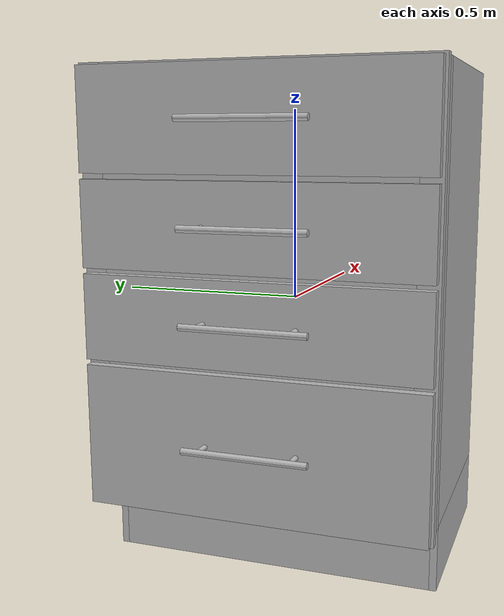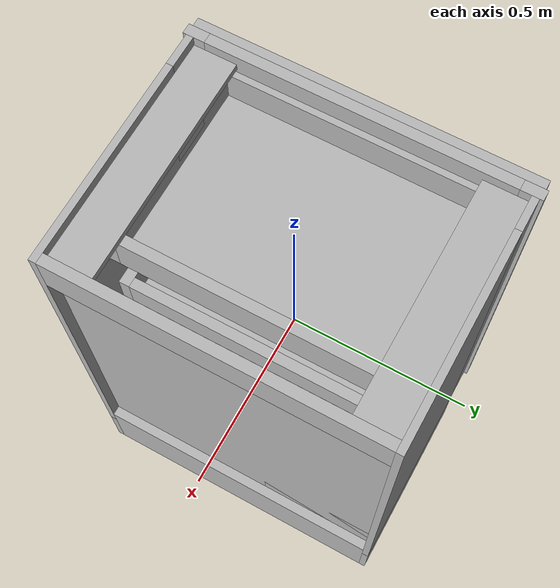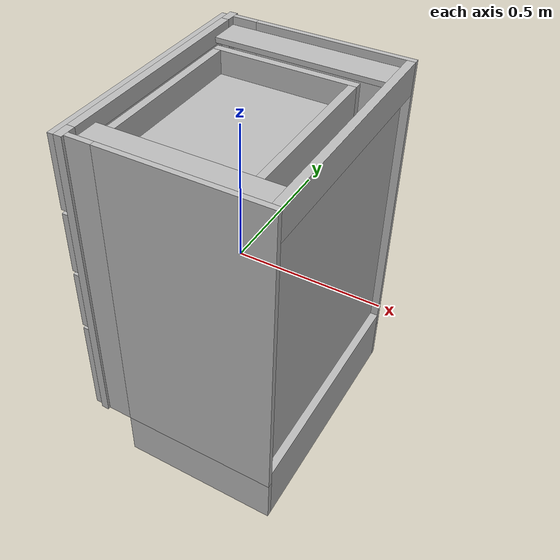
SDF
<sdf version="1.7">
  <model name="cabinet_1076">
    <link name="base_link">
      <inertial>
        <pose>0.0 0.0 0.0 0.0 0.0 0.0</pose>
        <mass>100</mass>
        <inertia>
          <ixx>27.945378620841662</ixx>
          <ixy>0</ixy>
          <ixz>0</ixz>
          <iyy>16.609441110241665</iyy>
          <iyz>0</iyz>
          <izz>32.59602664941666</izz>
        </inertia>
      </inertial>
      <self_collide>0</self_collide>
      <enable_wind>0</enable_wind>
      <kinematic>0</kinematic>
      <pose>0.0 0.0 0.0 0.0 0.0 0.0</pose>
      <gravity>1</gravity>
      <visual name="base_link_fixed_joint_lump__vertical_side_panel-83_visual_9">
        <pose>0.0 0.0 0.0 1.5708 0.0 -1.5708</pose>
        <geometry>
          <mesh>
            <scale>0.8 0.8 0.8</scale>
            <uri>model://cabinet_1076/textured_objs/original-15.obj</uri>
          </mesh>
        </geometry>
        <material>
          <shader type="pixel">
            <normal_map>__default__</normal_map>
          </shader>
        </material>
        <transparency>0</transparency>
        <cast_shadows>1</cast_shadows>
      </visual>
      <visual name="base_link_fixed_joint_lump__vertical_side_panel-82_visual_8">
        <pose>0.0 0.0 0.0 1.5708 0.0 -1.5708</pose>
        <geometry>
          <mesh>
            <scale>0.8 0.8 0.8</scale>
            <uri>model://cabinet_1076/textured_objs/original-10.obj</uri>
          </mesh>
        </geometry>
        <material>
          <shader type="pixel">
            <normal_map>__default__</normal_map>
          </shader>
        </material>
        <transparency>0</transparency>
        <cast_shadows>1</cast_shadows>
      </visual>
      <visual name="base_link_fixed_joint_lump__frame_horizontal_bar-78_visual_3">
        <pose>0.0 0.0 0.0 1.5708 0.0 -1.5708</pose>
        <geometry>
          <mesh>
            <scale>0.8 0.8 0.8</scale>
            <uri>model://cabinet_1076/textured_objs/original-20.obj</uri>
          </mesh>
        </geometry>
        <material>
          <shader type="pixel">
            <normal_map>__default__</normal_map>
          </shader>
        </material>
        <transparency>0</transparency>
        <cast_shadows>1</cast_shadows>
      </visual>
      <visual name="base_link_fixed_joint_lump__bottom_panel-85_visual_13">
        <pose>0.0 0.0 0.0 1.5708 0.0 -1.5708</pose>
        <geometry>
          <mesh>
            <scale>0.8 0.8 0.8</scale>
            <uri>model://cabinet_1076/textured_objs/original-8.obj</uri>
          </mesh>
        </geometry>
        <material>
          <shader type="pixel">
            <normal_map>__default__</normal_map>
          </shader>
        </material>
        <transparency>0</transparency>
        <cast_shadows>1</cast_shadows>
      </visual>
      <visual name="base_link_fixed_joint_lump__frame_horizontal_bar-87_visual_15">
        <pose>0.0 0.0 0.0 1.5708 0.0 -1.5708</pose>
        <geometry>
          <mesh>
            <scale>0.8 0.8 0.8</scale>
            <uri>model://cabinet_1076/textured_objs/original-4.obj</uri>
          </mesh>
        </geometry>
        <material>
          <shader type="pixel">
            <normal_map>__default__</normal_map>
          </shader>
        </material>
        <transparency>0</transparency>
        <cast_shadows>1</cast_shadows>
      </visual>
      <visual name="base_link_fixed_joint_lump__frame_horizontal_bar-80_visual_5">
        <pose>0.0 0.0 0.0 1.5708 0.0 -1.5708</pose>
        <geometry>
          <mesh>
            <scale>0.8 0.8 0.8</scale>
            <uri>model://cabinet_1076/textured_objs/original-22.obj</uri>
          </mesh>
        </geometry>
        <material>
          <shader type="pixel">
            <normal_map>__default__</normal_map>
          </shader>
        </material>
        <transparency>0</transparency>
        <cast_shadows>1</cast_shadows>
      </visual>
      <visual name="base_link_fixed_joint_lump__frame_vertical_bar-76_visual_1">
        <pose>0.0 0.0 0.0 1.5708 0.0 -1.5708</pose>
        <geometry>
          <mesh>
            <scale>0.8 0.8 0.8</scale>
            <uri>model://cabinet_1076/textured_objs/original-7.obj</uri>
          </mesh>
        </geometry>
        <material>
          <shader type="pixel">
            <normal_map>__default__</normal_map>
          </shader>
        </material>
        <transparency>0</transparency>
        <cast_shadows>1</cast_shadows>
      </visual>
      <visual name="base_link_fixed_joint_lump__vertical_side_panel-83_visual_10">
        <pose>0.0 0.0 0.0 1.5708 0.0 -1.5708</pose>
        <geometry>
          <mesh>
            <scale>0.8 0.8 0.8</scale>
            <uri>model://cabinet_1076/textured_objs/original-14.obj</uri>
          </mesh>
        </geometry>
        <material>
          <shader type="pixel">
            <normal_map>__default__</normal_map>
          </shader>
        </material>
        <transparency>0</transparency>
        <cast_shadows>1</cast_shadows>
      </visual>
      <visual name="base_link_fixed_joint_lump__frame_horizontal_bar-86_visual_14">
        <pose>0.0 0.0 0.0 1.5708 0.0 -1.5708</pose>
        <geometry>
          <mesh>
            <scale>0.8 0.8 0.8</scale>
            <uri>model://cabinet_1076/textured_objs/original-23.obj</uri>
          </mesh>
        </geometry>
        <material>
          <shader type="pixel">
            <normal_map>__default__</normal_map>
          </shader>
        </material>
        <transparency>0</transparency>
        <cast_shadows>1</cast_shadows>
      </visual>
      <visual name="base_link_fixed_joint_lump__bottom_panel-85_visual_12">
        <pose>0.0 0.0 0.0 1.5708 0.0 -1.5708</pose>
        <geometry>
          <mesh>
            <scale>0.8 0.8 0.8</scale>
            <uri>model://cabinet_1076/textured_objs/original-2.obj</uri>
          </mesh>
        </geometry>
        <material>
          <shader type="pixel">
            <normal_map>__default__</normal_map>
          </shader>
        </material>
        <transparency>0</transparency>
        <cast_shadows>1</cast_shadows>
      </visual>
      <visual name="base_link_fixed_joint_lump__back_panel-84_visual_11">
        <pose>0.0 0.0 0.0 1.5708 0.0 -1.5708</pose>
        <geometry>
          <mesh>
            <scale>0.8 0.8 0.8</scale>
            <uri>model://cabinet_1076/textured_objs/original-5.obj</uri>
          </mesh>
        </geometry>
        <material>
          <shader type="pixel">
            <normal_map>__default__</normal_map>
          </shader>
        </material>
        <transparency>0</transparency>
        <cast_shadows>1</cast_shadows>
      </visual>
      <visual name="base_link_fixed_joint_lump__base_side_panel-58_visual_20">
        <pose>0.0 0.0 0.0 1.5708 0.0 -1.5708</pose>
        <geometry>
          <mesh>
            <scale>0.8 0.8 0.8</scale>
            <uri>model://cabinet_1076/textured_objs/original-19.obj</uri>
          </mesh>
        </geometry>
        <material>
          <shader type="pixel">
            <normal_map>__default__</normal_map>
          </shader>
        </material>
        <transparency>0</transparency>
        <cast_shadows>1</cast_shadows>
      </visual>
      <visual name="base_link_fixed_joint_lump__frame_horizontal_bar-77_visual_2">
        <pose>0.0 0.0 0.0 1.5708 0.0 -1.5708</pose>
        <geometry>
          <mesh>
            <scale>0.8 0.8 0.8</scale>
            <uri>model://cabinet_1076/textured_objs/original-21.obj</uri>
          </mesh>
        </geometry>
        <material>
          <shader type="pixel">
            <normal_map>__default__</normal_map>
          </shader>
        </material>
        <transparency>0</transparency>
        <cast_shadows>1</cast_shadows>
      </visual>
      <visual name="base_link_fixed_joint_lump__base_side_panel-55_visual_17">
        <pose>0.0 0.0 0.0 1.5708 0.0 -1.5708</pose>
        <geometry>
          <mesh>
            <scale>0.8 0.8 0.8</scale>
            <uri>model://cabinet_1076/textured_objs/original-16.obj</uri>
          </mesh>
        </geometry>
        <material>
          <shader type="pixel">
            <normal_map>__default__</normal_map>
          </shader>
        </material>
        <transparency>0</transparency>
        <cast_shadows>1</cast_shadows>
      </visual>
      <visual name="base_link_fixed_joint_lump__base_side_panel-56_visual_18">
        <pose>0.0 0.0 0.0 1.5708 0.0 -1.5708</pose>
        <geometry>
          <mesh>
            <scale>0.8 0.8 0.8</scale>
            <uri>model://cabinet_1076/textured_objs/original-18.obj</uri>
          </mesh>
        </geometry>
        <material>
          <shader type="pixel">
            <normal_map>__default__</normal_map>
          </shader>
        </material>
        <transparency>0</transparency>
        <cast_shadows>1</cast_shadows>
      </visual>
      <visual name="base_link_fixed_joint_lump__vertical_side_panel-82_visual_7">
        <pose>0.0 0.0 0.0 1.5708 0.0 -1.5708</pose>
        <geometry>
          <mesh>
            <scale>0.8 0.8 0.8</scale>
            <uri>model://cabinet_1076/textured_objs/original-11.obj</uri>
          </mesh>
        </geometry>
        <material>
          <shader type="pixel">
            <normal_map>__default__</normal_map>
          </shader>
        </material>
        <transparency>0</transparency>
        <cast_shadows>1</cast_shadows>
      </visual>
      <visual name="base_link_fixed_joint_lump__base_side_panel-57_visual_19">
        <pose>0.0 0.0 0.0 1.5708 0.0 -1.5708</pose>
        <geometry>
          <mesh>
            <scale>0.8 0.8 0.8</scale>
            <uri>model://cabinet_1076/textured_objs/original-12.obj</uri>
          </mesh>
        </geometry>
        <material>
          <shader type="pixel">
            <normal_map>__default__</normal_map>
          </shader>
        </material>
        <transparency>0</transparency>
        <cast_shadows>1</cast_shadows>
      </visual>
      <visual name="base_link_fixed_joint_lump__other_leaf-89_visual_16">
        <pose>0.0 0.0 0.0 1.5708 0.0 -1.5708</pose>
        <geometry>
          <mesh>
            <scale>0.8 0.8 0.8</scale>
            <uri>model://cabinet_1076/textured_objs/original-88.obj</uri>
          </mesh>
        </geometry>
        <material>
          <shader type="pixel">
            <normal_map>__default__</normal_map>
          </shader>
        </material>
        <transparency>0</transparency>
        <cast_shadows>1</cast_shadows>
      </visual>
      <visual name="base_link_fixed_joint_lump__frame_horizontal_bar-81_visual_6">
        <pose>0.0 0.0 0.0 1.5708 0.0 -1.5708</pose>
        <geometry>
          <mesh>
            <scale>0.8 0.8 0.8</scale>
            <uri>model://cabinet_1076/textured_objs/original-17.obj</uri>
          </mesh>
        </geometry>
        <material>
          <shader type="pixel">
            <normal_map>__default__</normal_map>
          </shader>
        </material>
        <transparency>0</transparency>
        <cast_shadows>1</cast_shadows>
      </visual>
      <visual name="base_link_fixed_joint_lump__frame_horizontal_bar-79_visual_4">
        <pose>0.0 0.0 0.0 1.5708 0.0 -1.5708</pose>
        <geometry>
          <mesh>
            <scale>0.8 0.8 0.8</scale>
            <uri>model://cabinet_1076/textured_objs/original-6.obj</uri>
          </mesh>
        </geometry>
        <material>
          <shader type="pixel">
            <normal_map>__default__</normal_map>
          </shader>
        </material>
        <transparency>0</transparency>
        <cast_shadows>1</cast_shadows>
      </visual>
      <visual name="base_link_fixed_joint_lump__frame_vertical_bar-75_visual">
        <pose>0.0 0.0 0.0 1.5708 0.0 -1.5708</pose>
        <geometry>
          <mesh>
            <scale>0.8 0.8 0.8</scale>
            <uri>model://cabinet_1076/textured_objs/original-3.obj</uri>
          </mesh>
        </geometry>
        <material>
          <shader type="pixel">
            <normal_map>__default__</normal_map>
          </shader>
        </material>
        <transparency>0</transparency>
        <cast_shadows>1</cast_shadows>
      </visual>
      <collision name="base_link_fixed_joint_lump__link_4_collision_9">
        <laser_retro>0</laser_retro>
        <max_contacts>10</max_contacts>
        <pose>0.0 0.0 0.0 1.5708 0.0 -1.5708</pose>
        <geometry>
          <mesh>
            <uri>model://cabinet_1076/textured_objs/original-15.obj</uri>
            <scale>0.8 0.8 0.8</scale>
          </mesh>
        </geometry>
        <surface>
            <friction>
              <ode>
                <mu>10</mu>
                <mu2>10</mu2>
              </ode>
              <torsional>
                <coefficient>10.0</coefficient>
                <use_patch_radius>true</use_patch_radius>
                <patch_radius>0.1</patch_radius>
              </torsional>
            </friction>
          <bounce>
            <restitution_coefficient>0</restitution_coefficient>
            <threshold>1e+06</threshold>
          </bounce>
          <contact>
            <collide_without_contact>0</collide_without_contact>
            <collide_without_contact_bitmask>1</collide_without_contact_bitmask>
            <collide_bitmask>1</collide_bitmask>
            <ode>
              <soft_cfm>0</soft_cfm>
              <soft_erp>0.2</soft_erp>
              <kp>1e+13</kp>
              <kd>1</kd>
              <max_vel>0.001</max_vel>
              <min_depth>0</min_depth>
            </ode>
            <bullet>
              <split_impulse>1</split_impulse>
              <split_impulse_penetration_threshold>-0.01</split_impulse_penetration_threshold>
              <soft_cfm>0</soft_cfm>
              <soft_erp>0.2</soft_erp>
              <kp>1e+13</kp>
              <kd>1</kd>
            </bullet>
          </contact>
        </surface>
      </collision>
      <collision name="base_link_fixed_joint_lump__link_4_collision_18">
        <laser_retro>0</laser_retro>
        <max_contacts>10</max_contacts>
        <pose>0.0 0.0 0.0 1.5708 0.0 -1.5708</pose>
        <geometry>
          <mesh>
            <uri>model://cabinet_1076/textured_objs/original-18.obj</uri>
            <scale>0.8 0.8 0.8</scale>
          </mesh>
        </geometry>
        <surface>
            <friction>
              <ode>
                <mu>10</mu>
                <mu2>10</mu2>
              </ode>
              <torsional>
                <coefficient>10.0</coefficient>
                <use_patch_radius>true</use_patch_radius>
                <patch_radius>0.1</patch_radius>
              </torsional>
            </friction>
          <bounce>
            <restitution_coefficient>0</restitution_coefficient>
            <threshold>1e+06</threshold>
          </bounce>
          <contact>
            <collide_without_contact>0</collide_without_contact>
            <collide_without_contact_bitmask>1</collide_without_contact_bitmask>
            <collide_bitmask>1</collide_bitmask>
            <ode>
              <soft_cfm>0</soft_cfm>
              <soft_erp>0.2</soft_erp>
              <kp>1e+13</kp>
              <kd>1</kd>
              <max_vel>0.001</max_vel>
              <min_depth>0</min_depth>
            </ode>
            <bullet>
              <split_impulse>1</split_impulse>
              <split_impulse_penetration_threshold>-0.01</split_impulse_penetration_threshold>
              <soft_cfm>0</soft_cfm>
              <soft_erp>0.2</soft_erp>
              <kp>1e+13</kp>
              <kd>1</kd>
            </bullet>
          </contact>
        </surface>
      </collision>
      <collision name="base_link_fixed_joint_lump__link_4_collision_17">
        <laser_retro>0</laser_retro>
        <max_contacts>10</max_contacts>
        <pose>0.0 0.0 0.0 1.5708 0.0 -1.5708</pose>
        <geometry>
          <mesh>
            <uri>model://cabinet_1076/textured_objs/original-16.obj</uri>
            <scale>0.8 0.8 0.8</scale>
          </mesh>
        </geometry>
        <surface>
            <friction>
              <ode>
                <mu>10</mu>
                <mu2>10</mu2>
              </ode>
              <torsional>
                <coefficient>10.0</coefficient>
                <use_patch_radius>true</use_patch_radius>
                <patch_radius>0.1</patch_radius>
              </torsional>
            </friction>
          <bounce>
            <restitution_coefficient>0</restitution_coefficient>
            <threshold>1e+06</threshold>
          </bounce>
          <contact>
            <collide_without_contact>0</collide_without_contact>
            <collide_without_contact_bitmask>1</collide_without_contact_bitmask>
            <collide_bitmask>1</collide_bitmask>
            <ode>
              <soft_cfm>0</soft_cfm>
              <soft_erp>0.2</soft_erp>
              <kp>1e+13</kp>
              <kd>1</kd>
              <max_vel>0.001</max_vel>
              <min_depth>0</min_depth>
            </ode>
            <bullet>
              <split_impulse>1</split_impulse>
              <split_impulse_penetration_threshold>-0.01</split_impulse_penetration_threshold>
              <soft_cfm>0</soft_cfm>
              <soft_erp>0.2</soft_erp>
              <kp>1e+13</kp>
              <kd>1</kd>
            </bullet>
          </contact>
        </surface>
      </collision>
      <collision name="base_link_fixed_joint_lump__link_4_collision">
        <laser_retro>0</laser_retro>
        <max_contacts>10</max_contacts>
        <pose>0.0 0.0 0.0 1.5708 0.0 -1.5708</pose>
        <geometry>
          <mesh>
            <uri>model://cabinet_1076/textured_objs/original-3.obj</uri>
            <scale>0.8 0.8 0.8</scale>
          </mesh>
        </geometry>
        <surface>
            <friction>
              <ode>
                <mu>10</mu>
                <mu2>10</mu2>
              </ode>
              <torsional>
                <coefficient>10.0</coefficient>
                <use_patch_radius>true</use_patch_radius>
                <patch_radius>0.1</patch_radius>
              </torsional>
            </friction>
          <bounce>
            <restitution_coefficient>0</restitution_coefficient>
            <threshold>1e+06</threshold>
          </bounce>
          <contact>
            <collide_without_contact>0</collide_without_contact>
            <collide_without_contact_bitmask>1</collide_without_contact_bitmask>
            <collide_bitmask>1</collide_bitmask>
            <ode>
              <soft_cfm>0</soft_cfm>
              <soft_erp>0.2</soft_erp>
              <kp>1e+13</kp>
              <kd>1</kd>
              <max_vel>0.001</max_vel>
              <min_depth>0</min_depth>
            </ode>
            <bullet>
              <split_impulse>1</split_impulse>
              <split_impulse_penetration_threshold>-0.01</split_impulse_penetration_threshold>
              <soft_cfm>0</soft_cfm>
              <soft_erp>0.2</soft_erp>
              <kp>1e+13</kp>
              <kd>1</kd>
            </bullet>
          </contact>
        </surface>
      </collision>
      <collision name="base_link_fixed_joint_lump__link_4_collision_1">
        <laser_retro>0</laser_retro>
        <max_contacts>10</max_contacts>
        <pose>0.0 0.0 0.0 1.5708 0.0 -1.5708</pose>
        <geometry>
          <mesh>
            <uri>model://cabinet_1076/textured_objs/original-7.obj</uri>
            <scale>0.8 0.8 0.8</scale>
          </mesh>
        </geometry>
        <surface>
            <friction>
              <ode>
                <mu>10</mu>
                <mu2>10</mu2>
              </ode>
              <torsional>
                <coefficient>10.0</coefficient>
                <use_patch_radius>true</use_patch_radius>
                <patch_radius>0.1</patch_radius>
              </torsional>
            </friction>
          <bounce>
            <restitution_coefficient>0</restitution_coefficient>
            <threshold>1e+06</threshold>
          </bounce>
          <contact>
            <collide_without_contact>0</collide_without_contact>
            <collide_without_contact_bitmask>1</collide_without_contact_bitmask>
            <collide_bitmask>1</collide_bitmask>
            <ode>
              <soft_cfm>0</soft_cfm>
              <soft_erp>0.2</soft_erp>
              <kp>1e+13</kp>
              <kd>1</kd>
              <max_vel>0.001</max_vel>
              <min_depth>0</min_depth>
            </ode>
            <bullet>
              <split_impulse>1</split_impulse>
              <split_impulse_penetration_threshold>-0.01</split_impulse_penetration_threshold>
              <soft_cfm>0</soft_cfm>
              <soft_erp>0.2</soft_erp>
              <kp>1e+13</kp>
              <kd>1</kd>
            </bullet>
          </contact>
        </surface>
      </collision>
      <collision name="base_link_fixed_joint_lump__link_4_collision_5">
        <laser_retro>0</laser_retro>
        <max_contacts>10</max_contacts>
        <pose>0.0 0.0 0.0 1.5708 0.0 -1.5708</pose>
        <geometry>
          <mesh>
            <uri>model://cabinet_1076/textured_objs/original-22.obj</uri>
            <scale>0.8 0.8 0.8</scale>
          </mesh>
        </geometry>
        <surface>
            <friction>
              <ode>
                <mu>10</mu>
                <mu2>10</mu2>
              </ode>
              <torsional>
                <coefficient>10.0</coefficient>
                <use_patch_radius>true</use_patch_radius>
                <patch_radius>0.1</patch_radius>
              </torsional>
            </friction>
          <bounce>
            <restitution_coefficient>0</restitution_coefficient>
            <threshold>1e+06</threshold>
          </bounce>
          <contact>
            <collide_without_contact>0</collide_without_contact>
            <collide_without_contact_bitmask>1</collide_without_contact_bitmask>
            <collide_bitmask>1</collide_bitmask>
            <ode>
              <soft_cfm>0</soft_cfm>
              <soft_erp>0.2</soft_erp>
              <kp>1e+13</kp>
              <kd>1</kd>
              <max_vel>0.001</max_vel>
              <min_depth>0</min_depth>
            </ode>
            <bullet>
              <split_impulse>1</split_impulse>
              <split_impulse_penetration_threshold>-0.01</split_impulse_penetration_threshold>
              <soft_cfm>0</soft_cfm>
              <soft_erp>0.2</soft_erp>
              <kp>1e+13</kp>
              <kd>1</kd>
            </bullet>
          </contact>
        </surface>
      </collision>
      <collision name="base_link_fixed_joint_lump__link_4_collision_13">
        <laser_retro>0</laser_retro>
        <max_contacts>10</max_contacts>
        <pose>0.0 0.0 0.0 1.5708 0.0 -1.5708</pose>
        <geometry>
          <mesh>
            <uri>model://cabinet_1076/textured_objs/original-8.obj</uri>
            <scale>0.8 0.8 0.8</scale>
          </mesh>
        </geometry>
        <surface>
            <friction>
              <ode>
                <mu>10</mu>
                <mu2>10</mu2>
              </ode>
              <torsional>
                <coefficient>10.0</coefficient>
                <use_patch_radius>true</use_patch_radius>
                <patch_radius>0.1</patch_radius>
              </torsional>
            </friction>
          <bounce>
            <restitution_coefficient>0</restitution_coefficient>
            <threshold>1e+06</threshold>
          </bounce>
          <contact>
            <collide_without_contact>0</collide_without_contact>
            <collide_without_contact_bitmask>1</collide_without_contact_bitmask>
            <collide_bitmask>1</collide_bitmask>
            <ode>
              <soft_cfm>0</soft_cfm>
              <soft_erp>0.2</soft_erp>
              <kp>1e+13</kp>
              <kd>1</kd>
              <max_vel>0.001</max_vel>
              <min_depth>0</min_depth>
            </ode>
            <bullet>
              <split_impulse>1</split_impulse>
              <split_impulse_penetration_threshold>-0.01</split_impulse_penetration_threshold>
              <soft_cfm>0</soft_cfm>
              <soft_erp>0.2</soft_erp>
              <kp>1e+13</kp>
              <kd>1</kd>
            </bullet>
          </contact>
        </surface>
      </collision>
      <collision name="base_link_fixed_joint_lump__link_4_collision_8">
        <laser_retro>0</laser_retro>
        <max_contacts>10</max_contacts>
        <pose>0.0 0.0 0.0 1.5708 0.0 -1.5708</pose>
        <geometry>
          <mesh>
            <uri>model://cabinet_1076/textured_objs/original-10.obj</uri>
            <scale>0.8 0.8 0.8</scale>
          </mesh>
        </geometry>
        <surface>
            <friction>
              <ode>
                <mu>10</mu>
                <mu2>10</mu2>
              </ode>
              <torsional>
                <coefficient>10.0</coefficient>
                <use_patch_radius>true</use_patch_radius>
                <patch_radius>0.1</patch_radius>
              </torsional>
            </friction>
          <bounce>
            <restitution_coefficient>0</restitution_coefficient>
            <threshold>1e+06</threshold>
          </bounce>
          <contact>
            <collide_without_contact>0</collide_without_contact>
            <collide_without_contact_bitmask>1</collide_without_contact_bitmask>
            <collide_bitmask>1</collide_bitmask>
            <ode>
              <soft_cfm>0</soft_cfm>
              <soft_erp>0.2</soft_erp>
              <kp>1e+13</kp>
              <kd>1</kd>
              <max_vel>0.001</max_vel>
              <min_depth>0</min_depth>
            </ode>
            <bullet>
              <split_impulse>1</split_impulse>
              <split_impulse_penetration_threshold>-0.01</split_impulse_penetration_threshold>
              <soft_cfm>0</soft_cfm>
              <soft_erp>0.2</soft_erp>
              <kp>1e+13</kp>
              <kd>1</kd>
            </bullet>
          </contact>
        </surface>
      </collision>
      <collision name="base_link_fixed_joint_lump__link_4_collision_2">
        <laser_retro>0</laser_retro>
        <max_contacts>10</max_contacts>
        <pose>0.0 0.0 0.0 1.5708 0.0 -1.5708</pose>
        <geometry>
          <mesh>
            <uri>model://cabinet_1076/textured_objs/original-21.obj</uri>
            <scale>0.8 0.8 0.8</scale>
          </mesh>
        </geometry>
        <surface>
            <friction>
              <ode>
                <mu>10</mu>
                <mu2>10</mu2>
              </ode>
              <torsional>
                <coefficient>10.0</coefficient>
                <use_patch_radius>true</use_patch_radius>
                <patch_radius>0.1</patch_radius>
              </torsional>
            </friction>
          <bounce>
            <restitution_coefficient>0</restitution_coefficient>
            <threshold>1e+06</threshold>
          </bounce>
          <contact>
            <collide_without_contact>0</collide_without_contact>
            <collide_without_contact_bitmask>1</collide_without_contact_bitmask>
            <collide_bitmask>1</collide_bitmask>
            <ode>
              <soft_cfm>0</soft_cfm>
              <soft_erp>0.2</soft_erp>
              <kp>1e+13</kp>
              <kd>1</kd>
              <max_vel>0.001</max_vel>
              <min_depth>0</min_depth>
            </ode>
            <bullet>
              <split_impulse>1</split_impulse>
              <split_impulse_penetration_threshold>-0.01</split_impulse_penetration_threshold>
              <soft_cfm>0</soft_cfm>
              <soft_erp>0.2</soft_erp>
              <kp>1e+13</kp>
              <kd>1</kd>
            </bullet>
          </contact>
        </surface>
      </collision>
      <collision name="base_link_fixed_joint_lump__link_4_collision_11">
        <laser_retro>0</laser_retro>
        <max_contacts>10</max_contacts>
        <pose>0.0 0.0 0.0 1.5708 0.0 -1.5708</pose>
        <geometry>
          <mesh>
            <uri>model://cabinet_1076/textured_objs/original-5.obj</uri>
            <scale>0.8 0.8 0.8</scale>
          </mesh>
        </geometry>
        <surface>
            <friction>
              <ode>
                <mu>10</mu>
                <mu2>10</mu2>
              </ode>
              <torsional>
                <coefficient>10.0</coefficient>
                <use_patch_radius>true</use_patch_radius>
                <patch_radius>0.1</patch_radius>
              </torsional>
            </friction>
          <bounce>
            <restitution_coefficient>0</restitution_coefficient>
            <threshold>1e+06</threshold>
          </bounce>
          <contact>
            <collide_without_contact>0</collide_without_contact>
            <collide_without_contact_bitmask>1</collide_without_contact_bitmask>
            <collide_bitmask>1</collide_bitmask>
            <ode>
              <soft_cfm>0</soft_cfm>
              <soft_erp>0.2</soft_erp>
              <kp>1e+13</kp>
              <kd>1</kd>
              <max_vel>0.001</max_vel>
              <min_depth>0</min_depth>
            </ode>
            <bullet>
              <split_impulse>1</split_impulse>
              <split_impulse_penetration_threshold>-0.01</split_impulse_penetration_threshold>
              <soft_cfm>0</soft_cfm>
              <soft_erp>0.2</soft_erp>
              <kp>1e+13</kp>
              <kd>1</kd>
            </bullet>
          </contact>
        </surface>
      </collision>
      <collision name="base_link_fixed_joint_lump__link_4_collision_14">
        <laser_retro>0</laser_retro>
        <max_contacts>10</max_contacts>
        <pose>0.0 0.0 0.0 1.5708 0.0 -1.5708</pose>
        <geometry>
          <mesh>
            <uri>model://cabinet_1076/textured_objs/original-23.obj</uri>
            <scale>0.8 0.8 0.8</scale>
          </mesh>
        </geometry>
        <surface>
            <friction>
              <ode>
                <mu>10</mu>
                <mu2>10</mu2>
              </ode>
              <torsional>
                <coefficient>10.0</coefficient>
                <use_patch_radius>true</use_patch_radius>
                <patch_radius>0.1</patch_radius>
              </torsional>
            </friction>
          <bounce>
            <restitution_coefficient>0</restitution_coefficient>
            <threshold>1e+06</threshold>
          </bounce>
          <contact>
            <collide_without_contact>0</collide_without_contact>
            <collide_without_contact_bitmask>1</collide_without_contact_bitmask>
            <collide_bitmask>1</collide_bitmask>
            <ode>
              <soft_cfm>0</soft_cfm>
              <soft_erp>0.2</soft_erp>
              <kp>1e+13</kp>
              <kd>1</kd>
              <max_vel>0.001</max_vel>
              <min_depth>0</min_depth>
            </ode>
            <bullet>
              <split_impulse>1</split_impulse>
              <split_impulse_penetration_threshold>-0.01</split_impulse_penetration_threshold>
              <soft_cfm>0</soft_cfm>
              <soft_erp>0.2</soft_erp>
              <kp>1e+13</kp>
              <kd>1</kd>
            </bullet>
          </contact>
        </surface>
      </collision>
      <collision name="base_link_fixed_joint_lump__link_4_collision_7">
        <laser_retro>0</laser_retro>
        <max_contacts>10</max_contacts>
        <pose>0.0 0.0 0.0 1.5708 0.0 -1.5708</pose>
        <geometry>
          <mesh>
            <uri>model://cabinet_1076/textured_objs/original-11.obj</uri>
            <scale>0.8 0.8 0.8</scale>
          </mesh>
        </geometry>
        <surface>
            <friction>
              <ode>
                <mu>10</mu>
                <mu2>10</mu2>
              </ode>
              <torsional>
                <coefficient>10.0</coefficient>
                <use_patch_radius>true</use_patch_radius>
                <patch_radius>0.1</patch_radius>
              </torsional>
            </friction>
          <bounce>
            <restitution_coefficient>0</restitution_coefficient>
            <threshold>1e+06</threshold>
          </bounce>
          <contact>
            <collide_without_contact>0</collide_without_contact>
            <collide_without_contact_bitmask>1</collide_without_contact_bitmask>
            <collide_bitmask>1</collide_bitmask>
            <ode>
              <soft_cfm>0</soft_cfm>
              <soft_erp>0.2</soft_erp>
              <kp>1e+13</kp>
              <kd>1</kd>
              <max_vel>0.001</max_vel>
              <min_depth>0</min_depth>
            </ode>
            <bullet>
              <split_impulse>1</split_impulse>
              <split_impulse_penetration_threshold>-0.01</split_impulse_penetration_threshold>
              <soft_cfm>0</soft_cfm>
              <soft_erp>0.2</soft_erp>
              <kp>1e+13</kp>
              <kd>1</kd>
            </bullet>
          </contact>
        </surface>
      </collision>
      <collision name="base_link_fixed_joint_lump__link_4_collision_19">
        <laser_retro>0</laser_retro>
        <max_contacts>10</max_contacts>
        <pose>0.0 0.0 0.0 1.5708 0.0 -1.5708</pose>
        <geometry>
          <mesh>
            <uri>model://cabinet_1076/textured_objs/original-12.obj</uri>
            <scale>0.8 0.8 0.8</scale>
          </mesh>
        </geometry>
        <surface>
            <friction>
              <ode>
                <mu>10</mu>
                <mu2>10</mu2>
              </ode>
              <torsional>
                <coefficient>10.0</coefficient>
                <use_patch_radius>true</use_patch_radius>
                <patch_radius>0.1</patch_radius>
              </torsional>
            </friction>
          <bounce>
            <restitution_coefficient>0</restitution_coefficient>
            <threshold>1e+06</threshold>
          </bounce>
          <contact>
            <collide_without_contact>0</collide_without_contact>
            <collide_without_contact_bitmask>1</collide_without_contact_bitmask>
            <collide_bitmask>1</collide_bitmask>
            <ode>
              <soft_cfm>0</soft_cfm>
              <soft_erp>0.2</soft_erp>
              <kp>1e+13</kp>
              <kd>1</kd>
              <max_vel>0.001</max_vel>
              <min_depth>0</min_depth>
            </ode>
            <bullet>
              <split_impulse>1</split_impulse>
              <split_impulse_penetration_threshold>-0.01</split_impulse_penetration_threshold>
              <soft_cfm>0</soft_cfm>
              <soft_erp>0.2</soft_erp>
              <kp>1e+13</kp>
              <kd>1</kd>
            </bullet>
          </contact>
        </surface>
      </collision>
      <collision name="base_link_fixed_joint_lump__link_4_collision_15">
        <laser_retro>0</laser_retro>
        <max_contacts>10</max_contacts>
        <pose>0.0 0.0 0.0 1.5708 0.0 -1.5708</pose>
        <geometry>
          <mesh>
            <uri>model://cabinet_1076/textured_objs/original-4.obj</uri>
            <scale>0.8 0.8 0.8</scale>
          </mesh>
        </geometry>
        <surface>
            <friction>
              <ode>
                <mu>10</mu>
                <mu2>10</mu2>
              </ode>
              <torsional>
                <coefficient>10.0</coefficient>
                <use_patch_radius>true</use_patch_radius>
                <patch_radius>0.1</patch_radius>
              </torsional>
            </friction>
          <bounce>
            <restitution_coefficient>0</restitution_coefficient>
            <threshold>1e+06</threshold>
          </bounce>
          <contact>
            <collide_without_contact>0</collide_without_contact>
            <collide_without_contact_bitmask>1</collide_without_contact_bitmask>
            <collide_bitmask>1</collide_bitmask>
            <ode>
              <soft_cfm>0</soft_cfm>
              <soft_erp>0.2</soft_erp>
              <kp>1e+13</kp>
              <kd>1</kd>
              <max_vel>0.001</max_vel>
              <min_depth>0</min_depth>
            </ode>
            <bullet>
              <split_impulse>1</split_impulse>
              <split_impulse_penetration_threshold>-0.01</split_impulse_penetration_threshold>
              <soft_cfm>0</soft_cfm>
              <soft_erp>0.2</soft_erp>
              <kp>1e+13</kp>
              <kd>1</kd>
            </bullet>
          </contact>
        </surface>
      </collision>
      <collision name="base_link_fixed_joint_lump__link_4_collision_12">
        <laser_retro>0</laser_retro>
        <max_contacts>10</max_contacts>
        <pose>0.0 0.0 0.0 1.5708 0.0 -1.5708</pose>
        <geometry>
          <mesh>
            <uri>model://cabinet_1076/textured_objs/original-2.obj</uri>
            <scale>0.8 0.8 0.8</scale>
          </mesh>
        </geometry>
        <surface>
            <friction>
              <ode>
                <mu>10</mu>
                <mu2>10</mu2>
              </ode>
              <torsional>
                <coefficient>10.0</coefficient>
                <use_patch_radius>true</use_patch_radius>
                <patch_radius>0.1</patch_radius>
              </torsional>
            </friction>
          <bounce>
            <restitution_coefficient>0</restitution_coefficient>
            <threshold>1e+06</threshold>
          </bounce>
          <contact>
            <collide_without_contact>0</collide_without_contact>
            <collide_without_contact_bitmask>1</collide_without_contact_bitmask>
            <collide_bitmask>1</collide_bitmask>
            <ode>
              <soft_cfm>0</soft_cfm>
              <soft_erp>0.2</soft_erp>
              <kp>1e+13</kp>
              <kd>1</kd>
              <max_vel>0.001</max_vel>
              <min_depth>0</min_depth>
            </ode>
            <bullet>
              <split_impulse>1</split_impulse>
              <split_impulse_penetration_threshold>-0.01</split_impulse_penetration_threshold>
              <soft_cfm>0</soft_cfm>
              <soft_erp>0.2</soft_erp>
              <kp>1e+13</kp>
              <kd>1</kd>
            </bullet>
          </contact>
        </surface>
      </collision>
      <collision name="base_link_fixed_joint_lump__link_4_collision_3">
        <laser_retro>0</laser_retro>
        <max_contacts>10</max_contacts>
        <pose>0.0 0.0 0.0 1.5708 0.0 -1.5708</pose>
        <geometry>
          <mesh>
            <uri>model://cabinet_1076/textured_objs/original-20.obj</uri>
            <scale>0.8 0.8 0.8</scale>
          </mesh>
        </geometry>
        <surface>
            <friction>
              <ode>
                <mu>10</mu>
                <mu2>10</mu2>
              </ode>
              <torsional>
                <coefficient>10.0</coefficient>
                <use_patch_radius>true</use_patch_radius>
                <patch_radius>0.1</patch_radius>
              </torsional>
            </friction>
          <bounce>
            <restitution_coefficient>0</restitution_coefficient>
            <threshold>1e+06</threshold>
          </bounce>
          <contact>
            <collide_without_contact>0</collide_without_contact>
            <collide_without_contact_bitmask>1</collide_without_contact_bitmask>
            <collide_bitmask>1</collide_bitmask>
            <ode>
              <soft_cfm>0</soft_cfm>
              <soft_erp>0.2</soft_erp>
              <kp>1e+13</kp>
              <kd>1</kd>
              <max_vel>0.001</max_vel>
              <min_depth>0</min_depth>
            </ode>
            <bullet>
              <split_impulse>1</split_impulse>
              <split_impulse_penetration_threshold>-0.01</split_impulse_penetration_threshold>
              <soft_cfm>0</soft_cfm>
              <soft_erp>0.2</soft_erp>
              <kp>1e+13</kp>
              <kd>1</kd>
            </bullet>
          </contact>
        </surface>
      </collision>
      <collision name="base_link_fixed_joint_lump__link_4_collision_20">
        <laser_retro>0</laser_retro>
        <max_contacts>10</max_contacts>
        <pose>0.0 0.0 0.0 1.5708 0.0 -1.5708</pose>
        <geometry>
          <mesh>
            <uri>model://cabinet_1076/textured_objs/original-19.obj</uri>
            <scale>0.8 0.8 0.8</scale>
          </mesh>
        </geometry>
        <surface>
            <friction>
              <ode>
                <mu>10</mu>
                <mu2>10</mu2>
              </ode>
              <torsional>
                <coefficient>10.0</coefficient>
                <use_patch_radius>true</use_patch_radius>
                <patch_radius>0.1</patch_radius>
              </torsional>
            </friction>
          <bounce>
            <restitution_coefficient>0</restitution_coefficient>
            <threshold>1e+06</threshold>
          </bounce>
          <contact>
            <collide_without_contact>0</collide_without_contact>
            <collide_without_contact_bitmask>1</collide_without_contact_bitmask>
            <collide_bitmask>1</collide_bitmask>
            <ode>
              <soft_cfm>0</soft_cfm>
              <soft_erp>0.2</soft_erp>
              <kp>1e+13</kp>
              <kd>1</kd>
              <max_vel>0.001</max_vel>
              <min_depth>0</min_depth>
            </ode>
            <bullet>
              <split_impulse>1</split_impulse>
              <split_impulse_penetration_threshold>-0.01</split_impulse_penetration_threshold>
              <soft_cfm>0</soft_cfm>
              <soft_erp>0.2</soft_erp>
              <kp>1e+13</kp>
              <kd>1</kd>
            </bullet>
          </contact>
        </surface>
      </collision>
      <collision name="base_link_fixed_joint_lump__link_4_collision_10">
        <laser_retro>0</laser_retro>
        <max_contacts>10</max_contacts>
        <pose>0.0 0.0 0.0 1.5708 0.0 -1.5708</pose>
        <geometry>
          <mesh>
            <uri>model://cabinet_1076/textured_objs/original-14.obj</uri>
            <scale>0.8 0.8 0.8</scale>
          </mesh>
        </geometry>
        <surface>
            <friction>
              <ode>
                <mu>10</mu>
                <mu2>10</mu2>
              </ode>
              <torsional>
                <coefficient>10.0</coefficient>
                <use_patch_radius>true</use_patch_radius>
                <patch_radius>0.1</patch_radius>
              </torsional>
            </friction>
          <bounce>
            <restitution_coefficient>0</restitution_coefficient>
            <threshold>1e+06</threshold>
          </bounce>
          <contact>
            <collide_without_contact>0</collide_without_contact>
            <collide_without_contact_bitmask>1</collide_without_contact_bitmask>
            <collide_bitmask>1</collide_bitmask>
            <ode>
              <soft_cfm>0</soft_cfm>
              <soft_erp>0.2</soft_erp>
              <kp>1e+13</kp>
              <kd>1</kd>
              <max_vel>0.001</max_vel>
              <min_depth>0</min_depth>
            </ode>
            <bullet>
              <split_impulse>1</split_impulse>
              <split_impulse_penetration_threshold>-0.01</split_impulse_penetration_threshold>
              <soft_cfm>0</soft_cfm>
              <soft_erp>0.2</soft_erp>
              <kp>1e+13</kp>
              <kd>1</kd>
            </bullet>
          </contact>
        </surface>
      </collision>
      <collision name="base_link_fixed_joint_lump__link_4_collision_16">
        <laser_retro>0</laser_retro>
        <max_contacts>10</max_contacts>
        <pose>0.0 0.0 0.0 1.5708 0.0 -1.5708</pose>
        <geometry>
          <mesh>
            <uri>model://cabinet_1076/textured_objs/original-88.obj</uri>
            <scale>0.8 0.8 0.8</scale>
          </mesh>
        </geometry>
        <surface>
            <friction>
              <ode>
                <mu>10</mu>
                <mu2>10</mu2>
              </ode>
              <torsional>
                <coefficient>10.0</coefficient>
                <use_patch_radius>true</use_patch_radius>
                <patch_radius>0.1</patch_radius>
              </torsional>
            </friction>
          <bounce>
            <restitution_coefficient>0</restitution_coefficient>
            <threshold>1e+06</threshold>
          </bounce>
          <contact>
            <collide_without_contact>0</collide_without_contact>
            <collide_without_contact_bitmask>1</collide_without_contact_bitmask>
            <collide_bitmask>1</collide_bitmask>
            <ode>
              <soft_cfm>0</soft_cfm>
              <soft_erp>0.2</soft_erp>
              <kp>1e+13</kp>
              <kd>1</kd>
              <max_vel>0.001</max_vel>
              <min_depth>0</min_depth>
            </ode>
            <bullet>
              <split_impulse>1</split_impulse>
              <split_impulse_penetration_threshold>-0.01</split_impulse_penetration_threshold>
              <soft_cfm>0</soft_cfm>
              <soft_erp>0.2</soft_erp>
              <kp>1e+13</kp>
              <kd>1</kd>
            </bullet>
          </contact>
        </surface>
      </collision>
      <collision name="base_link_fixed_joint_lump__link_4_collision_4">
        <laser_retro>0</laser_retro>
        <max_contacts>10</max_contacts>
        <pose>0.0 0.0 0.0 1.5708 0.0 -1.5708</pose>
        <geometry>
          <mesh>
            <uri>model://cabinet_1076/textured_objs/original-6.obj</uri>
            <scale>0.8 0.8 0.8</scale>
          </mesh>
        </geometry>
        <surface>
            <friction>
              <ode>
                <mu>10</mu>
                <mu2>10</mu2>
              </ode>
              <torsional>
                <coefficient>10.0</coefficient>
                <use_patch_radius>true</use_patch_radius>
                <patch_radius>0.1</patch_radius>
              </torsional>
            </friction>
          <bounce>
            <restitution_coefficient>0</restitution_coefficient>
            <threshold>1e+06</threshold>
          </bounce>
          <contact>
            <collide_without_contact>0</collide_without_contact>
            <collide_without_contact_bitmask>1</collide_without_contact_bitmask>
            <collide_bitmask>1</collide_bitmask>
            <ode>
              <soft_cfm>0</soft_cfm>
              <soft_erp>0.2</soft_erp>
              <kp>1e+13</kp>
              <kd>1</kd>
              <max_vel>0.001</max_vel>
              <min_depth>0</min_depth>
            </ode>
            <bullet>
              <split_impulse>1</split_impulse>
              <split_impulse_penetration_threshold>-0.01</split_impulse_penetration_threshold>
              <soft_cfm>0</soft_cfm>
              <soft_erp>0.2</soft_erp>
              <kp>1e+13</kp>
              <kd>1</kd>
            </bullet>
          </contact>
        </surface>
      </collision>
      <collision name="base_link_fixed_joint_lump__link_4_collision_6">
        <laser_retro>0</laser_retro>
        <max_contacts>10</max_contacts>
        <pose>0.0 0.0 0.0 1.5708 0.0 -1.5708</pose>
        <geometry>
          <mesh>
            <uri>model://cabinet_1076/textured_objs/original-17.obj</uri>
            <scale>0.8 0.8 0.8</scale>
          </mesh>
        </geometry>
        <surface>
            <friction>
              <ode>
                <mu>10</mu>
                <mu2>10</mu2>
              </ode>
              <torsional>
                <coefficient>10.0</coefficient>
                <use_patch_radius>true</use_patch_radius>
                <patch_radius>0.1</patch_radius>
              </torsional>
            </friction>
          <bounce>
            <restitution_coefficient>0</restitution_coefficient>
            <threshold>1e+06</threshold>
          </bounce>
          <contact>
            <collide_without_contact>0</collide_without_contact>
            <collide_without_contact_bitmask>1</collide_without_contact_bitmask>
            <collide_bitmask>1</collide_bitmask>
            <ode>
              <soft_cfm>0</soft_cfm>
              <soft_erp>0.2</soft_erp>
              <kp>1e+13</kp>
              <kd>1</kd>
              <max_vel>0.001</max_vel>
              <min_depth>0</min_depth>
            </ode>
            <bullet>
              <split_impulse>1</split_impulse>
              <split_impulse_penetration_threshold>-0.01</split_impulse_penetration_threshold>
              <soft_cfm>0</soft_cfm>
              <soft_erp>0.2</soft_erp>
              <kp>1e+13</kp>
              <kd>1</kd>
            </bullet>
          </contact>
        </surface>
      </collision>
    </link>
    <link name="drawer_3">
      <pose>0.0 0.0 0.0 1.5708 0.0 -1.5708</pose>
      <inertial>
        <pose>0.0 0.0 0.0 0.0 0.0 0.0</pose>
        <mass>5</mass>
        <inertia>
          <ixx> 0.06598219020833333 </ixx>
          <ixy> 0 </ixy>
          <ixz> 0 </ixz>
          <iyy> 0.1509901320330833 </iyy>
          <iyz> 0 </iyz>
          <izz> 0.12100081564874995 </izz>
        </inertia>
      </inertial>
      <self_collide>0</self_collide>
      <enable_wind>0</enable_wind>
      <kinematic>0</kinematic>
      <visual name="drawer_3_fixed_joint_lump__drawer_back-50_visual_4">
        <pose>0.0 0.0 0.0 0.0 0.0 0.0</pose>
        <geometry>
          <mesh>
            <scale>0.8 0.8 0.8</scale>
            <uri>model://cabinet_1076/textured_objs/original-48.obj</uri>
          </mesh>
        </geometry>
        <material>
          <shader type="pixel" />
          <emissive>0 0 0 1</emissive>
        </material>
        <transparency>0</transparency>
        <cast_shadows>1</cast_shadows>
      </visual>
      <visual name="drawer_3_fixed_joint_lump__drawer_bottom-51_visual_5">
        <pose>0.0 0.0 0.0 0.0 0.0 0.0</pose>
        <geometry>
          <mesh>
            <scale>0.8 0.8 0.8</scale>
            <uri>model://cabinet_1076/textured_objs/original-46.obj</uri>
          </mesh>
        </geometry>
        <material>
          <shader type="pixel" />
          <emissive>0 0 0 1</emissive>
        </material>
        <transparency>0</transparency>
        <cast_shadows>1</cast_shadows>
      </visual>
      <visual name="drawer_3_fixed_joint_lump__drawer_side-48_visual_2">
        <pose>0.0 0.0 0.0 0.0 0.0 0.0</pose>
        <geometry>
          <mesh>
            <scale>0.8 0.8 0.8</scale>
            <uri>model://cabinet_1076/textured_objs/original-42.obj</uri>
          </mesh>
        </geometry>
        <material>
          <shader type="pixel" />
          <emissive>0 0 0 1</emissive>
        </material>
        <transparency>0</transparency>
        <cast_shadows>1</cast_shadows>
      </visual>
      <visual name="drawer_3_fixed_joint_lump__drawer_side-49_visual_3">
        <pose>0.0 0.0 0.0 0.0 0.0 0.0</pose>
        <geometry>
          <mesh>
            <scale>0.8 0.8 0.8</scale>
            <uri>model://cabinet_1076/textured_objs/original-47.obj</uri>
          </mesh>
        </geometry>
        <material>
          <shader type="pixel" />
          <emissive>0 0 0 1</emissive>
        </material>
        <transparency>0</transparency>
        <cast_shadows>1</cast_shadows>
      </visual>
      <visual name="drawer_3_fixed_joint_lump__other_leaf-53_visual_7">
        <pose>0.0 0.0 0.0 0.0 0.0 0.0</pose>
        <geometry>
          <mesh>
            <scale>0.8 0.8 0.8</scale>
            <uri>model://cabinet_1076/textured_objs/original-49.obj</uri>
          </mesh>
        </geometry>
        <material>
          <shader type="pixel" />
          <emissive>0 0 0 1</emissive>
        </material>
        <transparency>0</transparency>
        <cast_shadows>1</cast_shadows>
      </visual>
      <visual name="drawer_3_fixed_joint_lump__drawer_front-47_visual_1">
        <pose>0.0 0.0 0.0 0.0 0.0 0.0</pose>
        <geometry>
          <mesh>
            <scale>0.8 0.8 0.8</scale>
            <uri>model://cabinet_1076/textured_objs/original-43.obj</uri>
          </mesh>
        </geometry>
        <material>
          <shader type="pixel" />
          <emissive>0 0 0 1</emissive>
        </material>
        <transparency>0</transparency>
        <cast_shadows>1</cast_shadows>
      </visual>
      <visual name="drawer_3_fixed_joint_lump__drawer_front-46_visual">
        <pose>0.0 0.0 0.0 0.0 0.0 0.0</pose>
        <geometry>
          <mesh>
            <scale>0.8 0.8 0.8</scale>
            <uri>model://cabinet_1076/textured_objs/original-55.obj</uri>
          </mesh>
        </geometry>
        <material>
          <shader type="pixel" />
          <emissive>0 0 0 1</emissive>
        </material>
        <transparency>0</transparency>
        <cast_shadows>1</cast_shadows>
      </visual>
      <visual name="drawer_3_fixed_joint_lump__drawer_bottom-51_visual_6">
        <pose>0.0 0.0 0.0 0.0 0.0 0.0</pose>
        <geometry>
          <mesh>
            <scale>0.8 0.8 0.8</scale>
            <uri>model://cabinet_1076/textured_objs/original-45.obj</uri>
          </mesh>
        </geometry>
        <material>
          <shader type="pixel" />
          <emissive>0 0 0 1</emissive>
        </material>
        <transparency>0</transparency>
        <cast_shadows>1</cast_shadows>
      </visual>
      <collision name="drawer_3_collision_1">
        <laser_retro>0</laser_retro>
        <max_contacts>10</max_contacts>
        <pose>0.0 0.0 0.0 0.0 0.0 0.0</pose>
        <geometry>
          <mesh>
            <uri>model://cabinet_1076/textured_objs/original-43.obj</uri>
            <scale>0.8 0.8 0.8</scale>
          </mesh>
        </geometry>
        <surface>
            <friction>
              <ode>
                <mu>10</mu>
                <mu2>10</mu2>
              </ode>
              <torsional>
                <coefficient>10.0</coefficient>
                <use_patch_radius>true</use_patch_radius>
                <patch_radius>0.1</patch_radius>
              </torsional>
            </friction>
          <bounce>
            <restitution_coefficient>0</restitution_coefficient>
            <threshold>1e+06</threshold>
          </bounce>
          <contact>
            <collide_without_contact>0</collide_without_contact>
            <collide_without_contact_bitmask>1</collide_without_contact_bitmask>
            <collide_bitmask>1</collide_bitmask>
            <ode>
              <soft_cfm>0</soft_cfm>
              <soft_erp>0.2</soft_erp>
              <kp>1e+13</kp>
              <kd>1</kd>
              <max_vel>0.001</max_vel>
              <min_depth>0</min_depth>
            </ode>
            <bullet>
              <split_impulse>1</split_impulse>
              <split_impulse_penetration_threshold>-0.01</split_impulse_penetration_threshold>
              <soft_cfm>0</soft_cfm>
              <soft_erp>0.2</soft_erp>
              <kp>1e+13</kp>
              <kd>1</kd>
            </bullet>
          </contact>
        </surface>
      </collision>
      <collision name="drawer_3_collision_2">
        <laser_retro>0</laser_retro>
        <max_contacts>10</max_contacts>
        <pose>0.0 0.0 0.0 0.0 0.0 0.0</pose>
        <geometry>
          <mesh>
            <uri>model://cabinet_1076/textured_objs/original-42.obj</uri>
            <scale>0.8 0.8 0.8</scale>
          </mesh>
        </geometry>
        <surface>
            <friction>
              <ode>
                <mu>10</mu>
                <mu2>10</mu2>
              </ode>
              <torsional>
                <coefficient>10.0</coefficient>
                <use_patch_radius>true</use_patch_radius>
                <patch_radius>0.1</patch_radius>
              </torsional>
            </friction>
          <bounce>
            <restitution_coefficient>0</restitution_coefficient>
            <threshold>1e+06</threshold>
          </bounce>
          <contact>
            <collide_without_contact>0</collide_without_contact>
            <collide_without_contact_bitmask>1</collide_without_contact_bitmask>
            <collide_bitmask>1</collide_bitmask>
            <ode>
              <soft_cfm>0</soft_cfm>
              <soft_erp>0.2</soft_erp>
              <kp>1e+13</kp>
              <kd>1</kd>
              <max_vel>0.001</max_vel>
              <min_depth>0</min_depth>
            </ode>
            <bullet>
              <split_impulse>1</split_impulse>
              <split_impulse_penetration_threshold>-0.01</split_impulse_penetration_threshold>
              <soft_cfm>0</soft_cfm>
              <soft_erp>0.2</soft_erp>
              <kp>1e+13</kp>
              <kd>1</kd>
            </bullet>
          </contact>
        </surface>
      </collision>
      <collision name="drawer_3_collision_4">
        <laser_retro>0</laser_retro>
        <max_contacts>10</max_contacts>
        <pose>0.0 0.0 0.0 0.0 0.0 0.0</pose>
        <geometry>
          <mesh>
            <uri>model://cabinet_1076/textured_objs/original-48.obj</uri>
            <scale>0.8 0.8 0.8</scale>
          </mesh>
        </geometry>
        <surface>
            <friction>
              <ode>
                <mu>10</mu>
                <mu2>10</mu2>
              </ode>
              <torsional>
                <coefficient>10.0</coefficient>
                <use_patch_radius>true</use_patch_radius>
                <patch_radius>0.1</patch_radius>
              </torsional>
            </friction>
          <bounce>
            <restitution_coefficient>0</restitution_coefficient>
            <threshold>1e+06</threshold>
          </bounce>
          <contact>
            <collide_without_contact>0</collide_without_contact>
            <collide_without_contact_bitmask>1</collide_without_contact_bitmask>
            <collide_bitmask>1</collide_bitmask>
            <ode>
              <soft_cfm>0</soft_cfm>
              <soft_erp>0.2</soft_erp>
              <kp>1e+13</kp>
              <kd>1</kd>
              <max_vel>0.001</max_vel>
              <min_depth>0</min_depth>
            </ode>
            <bullet>
              <split_impulse>1</split_impulse>
              <split_impulse_penetration_threshold>-0.01</split_impulse_penetration_threshold>
              <soft_cfm>0</soft_cfm>
              <soft_erp>0.2</soft_erp>
              <kp>1e+13</kp>
              <kd>1</kd>
            </bullet>
          </contact>
        </surface>
      </collision>
      <collision name="drawer_3_collision_5">
        <laser_retro>0</laser_retro>
        <max_contacts>10</max_contacts>
        <pose>0.0 0.0 0.0 0.0 0.0 0.0</pose>
        <geometry>
          <mesh>
            <uri>model://cabinet_1076/textured_objs/original-46.obj</uri>
            <scale>0.8 0.8 0.8</scale>
          </mesh>
        </geometry>
        <surface>
            <friction>
              <ode>
                <mu>10</mu>
                <mu2>10</mu2>
              </ode>
              <torsional>
                <coefficient>10.0</coefficient>
                <use_patch_radius>true</use_patch_radius>
                <patch_radius>0.1</patch_radius>
              </torsional>
            </friction>
          <bounce>
            <restitution_coefficient>0</restitution_coefficient>
            <threshold>1e+06</threshold>
          </bounce>
          <contact>
            <collide_without_contact>0</collide_without_contact>
            <collide_without_contact_bitmask>1</collide_without_contact_bitmask>
            <collide_bitmask>1</collide_bitmask>
            <ode>
              <soft_cfm>0</soft_cfm>
              <soft_erp>0.2</soft_erp>
              <kp>1e+13</kp>
              <kd>1</kd>
              <max_vel>0.001</max_vel>
              <min_depth>0</min_depth>
            </ode>
            <bullet>
              <split_impulse>1</split_impulse>
              <split_impulse_penetration_threshold>-0.01</split_impulse_penetration_threshold>
              <soft_cfm>0</soft_cfm>
              <soft_erp>0.2</soft_erp>
              <kp>1e+13</kp>
              <kd>1</kd>
            </bullet>
          </contact>
        </surface>
      </collision>
      <collision name="drawer_3_collision_7">
        <laser_retro>0</laser_retro>
        <max_contacts>10</max_contacts>
        <pose>0.0 0.0 0.0 0.0 0.0 0.0</pose>
        <geometry>
          <mesh>
            <uri>model://cabinet_1076/textured_objs/original-49.obj</uri>
            <scale>0.8 0.8 0.8</scale>
          </mesh>
        </geometry>
        <surface>
            <friction>
              <ode>
                <mu>10</mu>
                <mu2>10</mu2>
              </ode>
              <torsional>
                <coefficient>10.0</coefficient>
                <use_patch_radius>true</use_patch_radius>
                <patch_radius>0.1</patch_radius>
              </torsional>
            </friction>
          <bounce>
            <restitution_coefficient>0</restitution_coefficient>
            <threshold>1e+06</threshold>
          </bounce>
          <contact>
            <collide_without_contact>0</collide_without_contact>
            <collide_without_contact_bitmask>1</collide_without_contact_bitmask>
            <collide_bitmask>1</collide_bitmask>
            <ode>
              <soft_cfm>0</soft_cfm>
              <soft_erp>0.2</soft_erp>
              <kp>1e+13</kp>
              <kd>1</kd>
              <max_vel>0.001</max_vel>
              <min_depth>0</min_depth>
            </ode>
            <bullet>
              <split_impulse>1</split_impulse>
              <split_impulse_penetration_threshold>-0.01</split_impulse_penetration_threshold>
              <soft_cfm>0</soft_cfm>
              <soft_erp>0.2</soft_erp>
              <kp>1e+13</kp>
              <kd>1</kd>
            </bullet>
          </contact>
        </surface>
      </collision>
      <collision name="drawer_3_collision_3">
        <laser_retro>0</laser_retro>
        <max_contacts>10</max_contacts>
        <pose>0.0 0.0 0.0 0.0 0.0 0.0</pose>
        <geometry>
          <mesh>
            <uri>model://cabinet_1076/textured_objs/original-47.obj</uri>
            <scale>0.8 0.8 0.8</scale>
          </mesh>
        </geometry>
        <surface>
            <friction>
              <ode>
                <mu>10</mu>
                <mu2>10</mu2>
              </ode>
              <torsional>
                <coefficient>10.0</coefficient>
                <use_patch_radius>true</use_patch_radius>
                <patch_radius>0.1</patch_radius>
              </torsional>
            </friction>
          <bounce>
            <restitution_coefficient>0</restitution_coefficient>
            <threshold>1e+06</threshold>
          </bounce>
          <contact>
            <collide_without_contact>0</collide_without_contact>
            <collide_without_contact_bitmask>1</collide_without_contact_bitmask>
            <collide_bitmask>1</collide_bitmask>
            <ode>
              <soft_cfm>0</soft_cfm>
              <soft_erp>0.2</soft_erp>
              <kp>1e+13</kp>
              <kd>1</kd>
              <max_vel>0.001</max_vel>
              <min_depth>0</min_depth>
            </ode>
            <bullet>
              <split_impulse>1</split_impulse>
              <split_impulse_penetration_threshold>-0.01</split_impulse_penetration_threshold>
              <soft_cfm>0</soft_cfm>
              <soft_erp>0.2</soft_erp>
              <kp>1e+13</kp>
              <kd>1</kd>
            </bullet>
          </contact>
        </surface>
      </collision>
      <collision name="drawer_3_collision_6">
        <laser_retro>0</laser_retro>
        <max_contacts>10</max_contacts>
        <pose>0.0 0.0 0.0 0.0 0.0 0.0</pose>
        <geometry>
          <mesh>
            <uri>model://cabinet_1076/textured_objs/original-45.obj</uri>
            <scale>0.8 0.8 0.8</scale>
          </mesh>
        </geometry>
        <surface>
            <friction>
              <ode>
                <mu>10</mu>
                <mu2>10</mu2>
              </ode>
              <torsional>
                <coefficient>10.0</coefficient>
                <use_patch_radius>true</use_patch_radius>
                <patch_radius>0.1</patch_radius>
              </torsional>
            </friction>
          <bounce>
            <restitution_coefficient>0</restitution_coefficient>
            <threshold>1e+06</threshold>
          </bounce>
          <contact>
            <collide_without_contact>0</collide_without_contact>
            <collide_without_contact_bitmask>1</collide_without_contact_bitmask>
            <collide_bitmask>1</collide_bitmask>
            <ode>
              <soft_cfm>0</soft_cfm>
              <soft_erp>0.2</soft_erp>
              <kp>1e+13</kp>
              <kd>1</kd>
              <max_vel>0.001</max_vel>
              <min_depth>0</min_depth>
            </ode>
            <bullet>
              <split_impulse>1</split_impulse>
              <split_impulse_penetration_threshold>-0.01</split_impulse_penetration_threshold>
              <soft_cfm>0</soft_cfm>
              <soft_erp>0.2</soft_erp>
              <kp>1e+13</kp>
              <kd>1</kd>
            </bullet>
          </contact>
        </surface>
      </collision>
      <collision name="drawer_3_collision">
        <laser_retro>0</laser_retro>
        <max_contacts>10</max_contacts>
        <pose>0.0 0.0 0.0 0.0 0.0 0.0</pose>
        <geometry>
          <mesh>
            <uri>model://cabinet_1076/textured_objs/original-55.obj</uri>
            <scale>0.8 0.8 0.8</scale>
          </mesh>
        </geometry>
        <surface>
            <friction>
              <ode>
                <mu>10</mu>
                <mu2>10</mu2>
              </ode>
              <torsional>
                <coefficient>10.0</coefficient>
                <use_patch_radius>true</use_patch_radius>
                <patch_radius>0.1</patch_radius>
              </torsional>
            </friction>
          <bounce>
            <restitution_coefficient>0</restitution_coefficient>
            <threshold>1e+06</threshold>
          </bounce>
          <contact>
            <collide_without_contact>0</collide_without_contact>
            <collide_without_contact_bitmask>1</collide_without_contact_bitmask>
            <collide_bitmask>1</collide_bitmask>
            <ode>
              <soft_cfm>0</soft_cfm>
              <soft_erp>0.2</soft_erp>
              <kp>1e+13</kp>
              <kd>1</kd>
              <max_vel>0.001</max_vel>
              <min_depth>0</min_depth>
            </ode>
            <bullet>
              <split_impulse>1</split_impulse>
              <split_impulse_penetration_threshold>-0.01</split_impulse_penetration_threshold>
              <soft_cfm>0</soft_cfm>
              <soft_erp>0.2</soft_erp>
              <kp>1e+13</kp>
              <kd>1</kd>
            </bullet>
          </contact>
        </surface>
      </collision>

    </link>
    <link name="drawer_2">
      <pose>0.0 0.0 0.0 1.5708 0.0 -1.5708</pose>
      <inertial>
        <pose>0.0 0.0 0.0 0.0 0.0 0.0</pose>
        <mass>5</mass>
        <inertia>
          <ixx>1</ixx>
          <ixy>0</ixy>
          <ixz>0</ixz>
          <iyy>1</iyy>
          <iyz>0</iyz>
          <izz>1</izz>
        </inertia>
      </inertial>
      <self_collide>0</self_collide>
      <enable_wind>0</enable_wind>
      <kinematic>0</kinematic>

      <visual name="drawer_2_fixed_joint_lump__drawer_side-39_visual_3">
        <pose>0.0 0.0 0.0 0.0 0.0 0.0</pose>
        <geometry>
          <mesh>
            <scale>0.8 0.8 0.8</scale>
            <uri>model://cabinet_1076/textured_objs/original-79.obj</uri>
          </mesh>
        </geometry>
        <material>
          <shader type="pixel" />
          <emissive>0 0 0 1</emissive>
        </material>
        <transparency>0</transparency>
        <cast_shadows>1</cast_shadows>
      </visual>
      <visual name="drawer_2_fixed_joint_lump__drawer_bottom-41_visual_5">
        <pose>0.0 0.0 0.0 0.0 0.0 0.0</pose>
        <geometry>
          <mesh>
            <scale>0.8 0.8 0.8</scale>
            <uri>model://cabinet_1076/textured_objs/original-78.obj</uri>
          </mesh>
        </geometry>
        <material>
          <shader type="pixel" />
          <emissive>0 0 0 1</emissive>
        </material>
        <transparency>0</transparency>
        <cast_shadows>1</cast_shadows>
      </visual>
      <visual name="drawer_2_fixed_joint_lump__drawer_front-37_visual_1">
        <pose>0.0 0.0 0.0 0.0 0.0 0.0</pose>
        <geometry>
          <mesh>
            <scale>0.8 0.8 0.8</scale>
            <uri>model://cabinet_1076/textured_objs/original-75.obj</uri>
          </mesh>
        </geometry>
        <material>
          <shader type="pixel" />
          <emissive>0 0 0 1</emissive>
        </material>
        <transparency>0</transparency>
        <cast_shadows>1</cast_shadows>
      </visual>
      <visual name="drawer_2_fixed_joint_lump__drawer_front-36_visual">
        <pose>0.0 0.0 0.0 0.0 0.0 0.0</pose>
        <geometry>
          <mesh>
            <scale>0.8 0.8 0.8</scale>
            <uri>model://cabinet_1076/textured_objs/original-87.obj</uri>
          </mesh>
        </geometry>
        <material>
          <shader type="pixel" />
          <emissive>0 0 0 1</emissive>
        </material>
        <transparency>0</transparency>
        <cast_shadows>1</cast_shadows>
      </visual>
      <visual name="drawer_2_fixed_joint_lump__drawer_back-40_visual_4">
        <pose>0.0 0.0 0.0 0.0 0.0 0.0</pose>
        <geometry>
          <mesh>
            <scale>0.8 0.8 0.8</scale>
            <uri>model://cabinet_1076/textured_objs/original-80.obj</uri>
          </mesh>
        </geometry>
        <material>
          <shader type="pixel" />
          <emissive>0 0 0 1</emissive>
        </material>
        <transparency>0</transparency>
        <cast_shadows>1</cast_shadows>
      </visual>
      <visual name="drawer_2_fixed_joint_lump__drawer_bottom-41_visual_6">
        <pose>0.0 0.0 0.0 0.0 0.0 0.0</pose>
        <geometry>
          <mesh>
            <scale>0.8 0.8 0.8</scale>
            <uri>model://cabinet_1076/textured_objs/original-77.obj</uri>
          </mesh>
        </geometry>
        <material>
          <shader type="pixel" />
          <emissive>0 0 0 1</emissive>
        </material>
        <transparency>0</transparency>
        <cast_shadows>1</cast_shadows>
      </visual>
      <visual name="drawer_2_fixed_joint_lump__drawer_side-38_visual_2">
        <pose>0.0 0.0 0.0 0.0 0.0 0.0</pose>
        <geometry>
          <mesh>
            <scale>0.8 0.8 0.8</scale>
            <uri>model://cabinet_1076/textured_objs/original-74.obj</uri>
          </mesh>
        </geometry>
        <material>
          <shader type="pixel" />
          <emissive>0 0 0 1</emissive>
        </material>
        <transparency>0</transparency>
        <cast_shadows>1</cast_shadows>
      </visual>
      <visual name="drawer_2_fixed_joint_lump__other_leaf-43_visual_7">
        <pose>0.0 0.0 0.0 0.0 0.0 0.0</pose>
        <geometry>
          <mesh>
            <scale>0.8 0.8 0.8</scale>
            <uri>model://cabinet_1076/textured_objs/original-81.obj</uri>
          </mesh>
        </geometry>
        <material>
          <shader type="pixel" />
          <emissive>0 0 0 1</emissive>
        </material>
        <transparency>0</transparency>
        <cast_shadows>1</cast_shadows>
      </visual>
      <collision name="drawer_2_collision_7">
        <laser_retro>0</laser_retro>
        <max_contacts>10</max_contacts>
        <pose>0.0 0.0 0.0 0.0 0.0 0.0</pose>
        <geometry>
          <mesh>
            <uri>model://cabinet_1076/textured_objs/original-81.obj</uri>
            <scale>0.8 0.8 0.8</scale>
          </mesh>
        </geometry>
        <surface>
            <friction>
              <ode>
                <mu>10</mu>
                <mu2>10</mu2>
              </ode>
              <torsional>
                <coefficient>10.0</coefficient>
                <use_patch_radius>true</use_patch_radius>
                <patch_radius>0.1</patch_radius>
              </torsional>
            </friction>
          <bounce>
            <restitution_coefficient>0</restitution_coefficient>
            <threshold>1e+06</threshold>
          </bounce>
          <contact>
            <collide_without_contact>0</collide_without_contact>
            <collide_without_contact_bitmask>1</collide_without_contact_bitmask>
            <collide_bitmask>1</collide_bitmask>
            <ode>
              <soft_cfm>0</soft_cfm>
              <soft_erp>0.2</soft_erp>
              <kp>1e+13</kp>
              <kd>1</kd>
              <max_vel>0.001</max_vel>
              <min_depth>0</min_depth>
            </ode>
            <bullet>
              <split_impulse>1</split_impulse>
              <split_impulse_penetration_threshold>-0.01</split_impulse_penetration_threshold>
              <soft_cfm>0</soft_cfm>
              <soft_erp>0.2</soft_erp>
              <kp>1e+13</kp>
              <kd>1</kd>
            </bullet>
          </contact>
        </surface>
      </collision>
      <collision name="drawer_2_collision_4">
        <laser_retro>0</laser_retro>
        <max_contacts>10</max_contacts>
        <pose>0.0 0.0 0.0 0.0 0.0 0.0</pose>
        <geometry>
          <mesh>
            <uri>model://cabinet_1076/textured_objs/original-80.obj</uri>
            <scale>0.8 0.8 0.8</scale>
          </mesh>
        </geometry>
        <surface>
            <friction>
              <ode>
                <mu>10</mu>
                <mu2>10</mu2>
              </ode>
              <torsional>
                <coefficient>10.0</coefficient>
                <use_patch_radius>true</use_patch_radius>
                <patch_radius>0.1</patch_radius>
              </torsional>
            </friction>
          <bounce>
            <restitution_coefficient>0</restitution_coefficient>
            <threshold>1e+06</threshold>
          </bounce>
          <contact>
            <collide_without_contact>0</collide_without_contact>
            <collide_without_contact_bitmask>1</collide_without_contact_bitmask>
            <collide_bitmask>1</collide_bitmask>
            <ode>
              <soft_cfm>0</soft_cfm>
              <soft_erp>0.2</soft_erp>
              <kp>1e+13</kp>
              <kd>1</kd>
              <max_vel>0.001</max_vel>
              <min_depth>0</min_depth>
            </ode>
            <bullet>
              <split_impulse>1</split_impulse>
              <split_impulse_penetration_threshold>-0.01</split_impulse_penetration_threshold>
              <soft_cfm>0</soft_cfm>
              <soft_erp>0.2</soft_erp>
              <kp>1e+13</kp>
              <kd>1</kd>
            </bullet>
          </contact>
        </surface>
      </collision>
      <collision name="drawer_2_collision_5">
        <laser_retro>0</laser_retro>
        <max_contacts>10</max_contacts>
        <pose>0.0 0.0 0.0 0.0 0.0 0.0</pose>
        <geometry>
          <mesh>
            <uri>model://cabinet_1076/textured_objs/original-78.obj</uri>
            <scale>0.8 0.8 0.8</scale>
          </mesh>
        </geometry>
        <surface>
            <friction>
              <ode>
                <mu>10</mu>
                <mu2>10</mu2>
              </ode>
              <torsional>
                <coefficient>10.0</coefficient>
                <use_patch_radius>true</use_patch_radius>
                <patch_radius>0.1</patch_radius>
              </torsional>
            </friction>
          <bounce>
            <restitution_coefficient>0</restitution_coefficient>
            <threshold>1e+06</threshold>
          </bounce>
          <contact>
            <collide_without_contact>0</collide_without_contact>
            <collide_without_contact_bitmask>1</collide_without_contact_bitmask>
            <collide_bitmask>1</collide_bitmask>
            <ode>
              <soft_cfm>0</soft_cfm>
              <soft_erp>0.2</soft_erp>
              <kp>1e+13</kp>
              <kd>1</kd>
              <max_vel>0.001</max_vel>
              <min_depth>0</min_depth>
            </ode>
            <bullet>
              <split_impulse>1</split_impulse>
              <split_impulse_penetration_threshold>-0.01</split_impulse_penetration_threshold>
              <soft_cfm>0</soft_cfm>
              <soft_erp>0.2</soft_erp>
              <kp>1e+13</kp>
              <kd>1</kd>
            </bullet>
          </contact>
        </surface>
      </collision>
      <collision name="drawer_2_collision_1">
        <laser_retro>0</laser_retro>
        <max_contacts>10</max_contacts>
        <pose>0.0 0.0 0.0 0.0 0.0 0.0</pose>
        <geometry>
          <mesh>
            <uri>model://cabinet_1076/textured_objs/original-75.obj</uri>
            <scale>0.8 0.8 0.8</scale>
          </mesh>
        </geometry>
        <surface>
            <friction>
              <ode>
                <mu>10</mu>
                <mu2>10</mu2>
              </ode>
              <torsional>
                <coefficient>10.0</coefficient>
                <use_patch_radius>true</use_patch_radius>
                <patch_radius>0.1</patch_radius>
              </torsional>
            </friction>
          <bounce>
            <restitution_coefficient>0</restitution_coefficient>
            <threshold>1e+06</threshold>
          </bounce>
          <contact>
            <collide_without_contact>0</collide_without_contact>
            <collide_without_contact_bitmask>1</collide_without_contact_bitmask>
            <collide_bitmask>1</collide_bitmask>
            <ode>
              <soft_cfm>0</soft_cfm>
              <soft_erp>0.2</soft_erp>
              <kp>1e+13</kp>
              <kd>1</kd>
              <max_vel>0.001</max_vel>
              <min_depth>0</min_depth>
            </ode>
            <bullet>
              <split_impulse>1</split_impulse>
              <split_impulse_penetration_threshold>-0.01</split_impulse_penetration_threshold>
              <soft_cfm>0</soft_cfm>
              <soft_erp>0.2</soft_erp>
              <kp>1e+13</kp>
              <kd>1</kd>
            </bullet>
          </contact>
        </surface>
      </collision>
      <collision name="drawer_2_collision_3">
        <laser_retro>0</laser_retro>
        <max_contacts>10</max_contacts>
        <pose>0.0 0.0 0.0 0.0 0.0 0.0</pose>
        <geometry>
          <mesh>
            <uri>model://cabinet_1076/textured_objs/original-79.obj</uri>
            <scale>0.8 0.8 0.8</scale>
          </mesh>
        </geometry>
        <surface>
            <friction>
              <ode>
                <mu>10</mu>
                <mu2>10</mu2>
              </ode>
              <torsional>
                <coefficient>10.0</coefficient>
                <use_patch_radius>true</use_patch_radius>
                <patch_radius>0.1</patch_radius>
              </torsional>
            </friction>
          <bounce>
            <restitution_coefficient>0</restitution_coefficient>
            <threshold>1e+06</threshold>
          </bounce>
          <contact>
            <collide_without_contact>0</collide_without_contact>
            <collide_without_contact_bitmask>1</collide_without_contact_bitmask>
            <collide_bitmask>1</collide_bitmask>
            <ode>
              <soft_cfm>0</soft_cfm>
              <soft_erp>0.2</soft_erp>
              <kp>1e+13</kp>
              <kd>1</kd>
              <max_vel>0.001</max_vel>
              <min_depth>0</min_depth>
            </ode>
            <bullet>
              <split_impulse>1</split_impulse>
              <split_impulse_penetration_threshold>-0.01</split_impulse_penetration_threshold>
              <soft_cfm>0</soft_cfm>
              <soft_erp>0.2</soft_erp>
              <kp>1e+13</kp>
              <kd>1</kd>
            </bullet>
          </contact>
        </surface>
      </collision>
      <collision name="drawer_2_collision_6">
        <laser_retro>0</laser_retro>
        <max_contacts>10</max_contacts>
        <pose>0.0 0.0 0.0 0.0 0.0 0.0</pose>
        <geometry>
          <mesh>
            <uri>model://cabinet_1076/textured_objs/original-77.obj</uri>
            <scale>0.8 0.8 0.8</scale>
          </mesh>
        </geometry>
        <surface>
            <friction>
              <ode>
                <mu>10</mu>
                <mu2>10</mu2>
              </ode>
              <torsional>
                <coefficient>10.0</coefficient>
                <use_patch_radius>true</use_patch_radius>
                <patch_radius>0.1</patch_radius>
              </torsional>
            </friction>
          <bounce>
            <restitution_coefficient>0</restitution_coefficient>
            <threshold>1e+06</threshold>
          </bounce>
          <contact>
            <collide_without_contact>0</collide_without_contact>
            <collide_without_contact_bitmask>1</collide_without_contact_bitmask>
            <collide_bitmask>1</collide_bitmask>
            <ode>
              <soft_cfm>0</soft_cfm>
              <soft_erp>0.2</soft_erp>
              <kp>1e+13</kp>
              <kd>1</kd>
              <max_vel>0.001</max_vel>
              <min_depth>0</min_depth>
            </ode>
            <bullet>
              <split_impulse>1</split_impulse>
              <split_impulse_penetration_threshold>-0.01</split_impulse_penetration_threshold>
              <soft_cfm>0</soft_cfm>
              <soft_erp>0.2</soft_erp>
              <kp>1e+13</kp>
              <kd>1</kd>
            </bullet>
          </contact>
        </surface>
      </collision>
      <collision name="drawer_2_collision_2">
        <laser_retro>0</laser_retro>
        <max_contacts>10</max_contacts>
        <pose>0.0 0.0 0.0 0.0 0.0 0.0</pose>
        <geometry>
          <mesh>
            <uri>model://cabinet_1076/textured_objs/original-74.obj</uri>
            <scale>0.8 0.8 0.8</scale>
          </mesh>
        </geometry>
        <surface>
            <friction>
              <ode>
                <mu>10</mu>
                <mu2>10</mu2>
              </ode>
              <torsional>
                <coefficient>10.0</coefficient>
                <use_patch_radius>true</use_patch_radius>
                <patch_radius>0.1</patch_radius>
              </torsional>
            </friction>
          <bounce>
            <restitution_coefficient>0</restitution_coefficient>
            <threshold>1e+06</threshold>
          </bounce>
          <contact>
            <collide_without_contact>0</collide_without_contact>
            <collide_without_contact_bitmask>1</collide_without_contact_bitmask>
            <collide_bitmask>1</collide_bitmask>
            <ode>
              <soft_cfm>0</soft_cfm>
              <soft_erp>0.2</soft_erp>
              <kp>1e+13</kp>
              <kd>1</kd>
              <max_vel>0.001</max_vel>
              <min_depth>0</min_depth>
            </ode>
            <bullet>
              <split_impulse>1</split_impulse>
              <split_impulse_penetration_threshold>-0.01</split_impulse_penetration_threshold>
              <soft_cfm>0</soft_cfm>
              <soft_erp>0.2</soft_erp>
              <kp>1e+13</kp>
              <kd>1</kd>
            </bullet>
          </contact>
        </surface>
      </collision>
      <collision name="drawer_2_collision">
        <laser_retro>0</laser_retro>
        <max_contacts>10</max_contacts>
        <pose>0.0 0.0 0.0 0.0 0.0 0.0</pose>
        <geometry>
          <mesh>
            <uri>model://cabinet_1076/textured_objs/original-87.obj</uri>
            <scale>0.8 0.8 0.8</scale>
          </mesh>
        </geometry>
        <surface>
            <friction>
              <ode>
                <mu>10</mu>
                <mu2>10</mu2>
              </ode>
              <torsional>
                <coefficient>10.0</coefficient>
                <use_patch_radius>true</use_patch_radius>
                <patch_radius>0.1</patch_radius>
              </torsional>
            </friction>
          <bounce>
            <restitution_coefficient>0</restitution_coefficient>
            <threshold>1e+06</threshold>
          </bounce>
          <contact>
            <collide_without_contact>0</collide_without_contact>
            <collide_without_contact_bitmask>1</collide_without_contact_bitmask>
            <collide_bitmask>1</collide_bitmask>
            <ode>
              <soft_cfm>0</soft_cfm>
              <soft_erp>0.2</soft_erp>
              <kp>1e+13</kp>
              <kd>1</kd>
              <max_vel>0.001</max_vel>
              <min_depth>0</min_depth>
            </ode>
            <bullet>
              <split_impulse>1</split_impulse>
              <split_impulse_penetration_threshold>-0.01</split_impulse_penetration_threshold>
              <soft_cfm>0</soft_cfm>
              <soft_erp>0.2</soft_erp>
              <kp>1e+13</kp>
              <kd>1</kd>
            </bullet>
          </contact>
        </surface>
      </collision>
    </link>
    <link name="drawer_1">
      <pose>0.0 0.0 0.0 1.5708 0.0 -1.5708</pose>
      <inertial>
        <pose>0.0 0.0 0.0 0.0 0.0 0.0</pose>
        <mass>5</mass>
        <inertia>
          <ixx>0.05435549562616668</ixx>
          <ixy>0</ixy>
          <ixz>0</ixz>
          <iyy>0.1509900055608333</iyy>
          <iyz>0</iyz>
          <izz>0.10937424753883329</izz>
        </inertia>
      </inertial>
      <self_collide>0</self_collide>
      <enable_wind>0</enable_wind>
      <kinematic>0</kinematic>

      <visual name="drawer_1_fixed_joint_lump__drawer_bottom-31_visual_6">
        <pose>0.0 0.0 0.0 0.0 0.0 0.0</pose>
        <geometry>
          <mesh>
            <scale>0.8 0.8 0.8</scale>
            <uri>model://cabinet_1076/textured_objs/original-61.obj</uri>
          </mesh>
        </geometry>
        <material>
          <shader type="pixel" />
          <emissive>0 0 0 1</emissive>
        </material>
        <transparency>0</transparency>
        <cast_shadows>1</cast_shadows>
      </visual>

      <visual name="drawer_1_fixed_joint_lump__other_leaf-33_visual_7">
        <pose>0.0 0.0 0.0 0.0 0.0 0.0</pose>
        <geometry>
          <mesh>
            <scale>0.8 0.8 0.8</scale>
            <uri>model://cabinet_1076/textured_objs/original-65.obj</uri>
          </mesh>
        </geometry>
        <material>
          <shader type="pixel" />
          <emissive>0 0 0 1</emissive>
        </material>
        <transparency>0</transparency>
        <cast_shadows>1</cast_shadows>
      </visual>
      <visual name="drawer_1_fixed_joint_lump__drawer_front-26_visual">
        <pose>0.0 0.0 0.0 0.0 0.0 0.0</pose>
        <geometry>
          <mesh>
            <scale>0.8 0.8 0.8</scale>
            <uri>model://cabinet_1076/textured_objs/original-59.obj</uri>
          </mesh>
        </geometry>
        <material>
          <shader type="pixel" />
          <emissive>0 0 0 1</emissive>
        </material>
        <transparency>0</transparency>
        <cast_shadows>1</cast_shadows>
      </visual>
      <visual name="drawer_1_fixed_joint_lump__drawer_back-30_visual_4">
        <pose>0.0 0.0 0.0 0.0 0.0 0.0</pose>
        <geometry>
          <mesh>
            <scale>0.8 0.8 0.8</scale>
            <uri>model://cabinet_1076/textured_objs/original-64.obj</uri>
          </mesh>
        </geometry>
        <material>
          <shader type="pixel" />
          <emissive>0 0 0 1</emissive>
        </material>
        <transparency>0</transparency>
        <cast_shadows>1</cast_shadows>
      </visual>
      <visual name="drawer_1_fixed_joint_lump__drawer_bottom-31_visual_5">
        <pose>0.0 0.0 0.0 0.0 0.0 0.0</pose>
        <geometry>
          <mesh>
            <scale>0.8 0.8 0.8</scale>
            <uri>model://cabinet_1076/textured_objs/original-62.obj</uri>
          </mesh>
        </geometry>
        <material>
          <shader type="pixel" />
          <emissive>0 0 0 1</emissive>
        </material>
        <transparency>0</transparency>
        <cast_shadows>1</cast_shadows>
      </visual>
      <visual name="drawer_1_fixed_joint_lump__drawer_front-27_visual_1">
        <pose>0.0 0.0 0.0 0.0 0.0 0.0</pose>
        <geometry>
          <mesh>
            <scale>0.8 0.8 0.8</scale>
            <uri>model://cabinet_1076/textured_objs/original-71.obj</uri>
          </mesh>
        </geometry>
        <material>
          <shader type="pixel" />
          <emissive>0 0 0 1</emissive>
        </material>
        <transparency>0</transparency>
        <cast_shadows>1</cast_shadows>
      </visual>
      <visual name="drawer_1_fixed_joint_lump__drawer_side-28_visual_2">
        <pose>0.0 0.0 0.0 0.0 0.0 0.0</pose>
        <geometry>
          <mesh>
            <scale>0.8 0.8 0.8</scale>
            <uri>model://cabinet_1076/textured_objs/original-58.obj</uri>
          </mesh>
        </geometry>
        <material>
          <shader type="pixel" />
          <emissive>0 0 0 1</emissive>
        </material>
        <transparency>0</transparency>
        <cast_shadows>1</cast_shadows>
      </visual>
      <visual name="drawer_1_fixed_joint_lump__drawer_side-29_visual_3">
        <pose>0.0 0.0 0.0 0.0 0.0 0.0</pose>
        <geometry>
          <mesh>
            <scale>0.8 0.8 0.8</scale>
            <uri>model://cabinet_1076/textured_objs/original-63.obj</uri>
          </mesh>
        </geometry>
        <material>
          <shader type="pixel" />
          <emissive>0 0 0 1</emissive>
        </material>
        <transparency>0</transparency>
        <cast_shadows>1</cast_shadows>
      </visual>
      <collision name="drawer_1_collision">
        <laser_retro>0</laser_retro>
        <max_contacts>10</max_contacts>
        <pose>0.0 0.0 0.0 0.0 0.0 0.0</pose>
        <geometry>
          <mesh>
            <uri>model://cabinet_1076/textured_objs/original-59.obj</uri>
            <scale>0.8 0.8 0.8</scale>
          </mesh>
        </geometry>
        <surface>
            <friction>
              <ode>
                <mu>10</mu>
                <mu2>10</mu2>
              </ode>
              <torsional>
                <coefficient>10.0</coefficient>
                <use_patch_radius>true</use_patch_radius>
                <patch_radius>0.1</patch_radius>
              </torsional>
            </friction>
          <bounce>
            <restitution_coefficient>0</restitution_coefficient>
            <threshold>1e+06</threshold>
          </bounce>
          <contact>
            <collide_without_contact>0</collide_without_contact>
            <collide_without_contact_bitmask>1</collide_without_contact_bitmask>
            <collide_bitmask>1</collide_bitmask>
            <ode>
              <soft_cfm>0</soft_cfm>
              <soft_erp>0.2</soft_erp>
              <kp>1e+13</kp>
              <kd>1</kd>
              <max_vel>0.001</max_vel>
              <min_depth>0</min_depth>
            </ode>
            <bullet>
              <split_impulse>1</split_impulse>
              <split_impulse_penetration_threshold>-0.01</split_impulse_penetration_threshold>
              <soft_cfm>0</soft_cfm>
              <soft_erp>0.2</soft_erp>
              <kp>1e+13</kp>
              <kd>1</kd>
            </bullet>
          </contact>
        </surface>
      </collision>
      <collision name="drawer_1_collision_5">
        <laser_retro>0</laser_retro>
        <max_contacts>10</max_contacts>
        <pose>0.0 0.0 0.0 0.0 0.0 0.0</pose>
        <geometry>
          <mesh>
            <uri>model://cabinet_1076/textured_objs/original-62.obj</uri>
            <scale>0.8 0.8 0.8</scale>
          </mesh>
        </geometry>
        <surface>
            <friction>
              <ode>
                <mu>10</mu>
                <mu2>10</mu2>
              </ode>
              <torsional>
                <coefficient>10.0</coefficient>
                <use_patch_radius>true</use_patch_radius>
                <patch_radius>0.1</patch_radius>
              </torsional>
            </friction>
          <bounce>
            <restitution_coefficient>0</restitution_coefficient>
            <threshold>1e+06</threshold>
          </bounce>
          <contact>
            <collide_without_contact>0</collide_without_contact>
            <collide_without_contact_bitmask>1</collide_without_contact_bitmask>
            <collide_bitmask>1</collide_bitmask>
            <ode>
              <soft_cfm>0</soft_cfm>
              <soft_erp>0.2</soft_erp>
              <kp>1e+13</kp>
              <kd>1</kd>
              <max_vel>0.001</max_vel>
              <min_depth>0</min_depth>
            </ode>
            <bullet>
              <split_impulse>1</split_impulse>
              <split_impulse_penetration_threshold>-0.01</split_impulse_penetration_threshold>
              <soft_cfm>0</soft_cfm>
              <soft_erp>0.2</soft_erp>
              <kp>1e+13</kp>
              <kd>1</kd>
            </bullet>
          </contact>
        </surface>
      </collision>
      <collision name="drawer_1_collision_4">
        <laser_retro>0</laser_retro>
        <max_contacts>10</max_contacts>
        <pose>0.0 0.0 0.0 0.0 0.0 0.0</pose>
        <geometry>
          <mesh>
            <uri>model://cabinet_1076/textured_objs/original-64.obj</uri>
            <scale>0.8 0.8 0.8</scale>
          </mesh>
        </geometry>
        <surface>
            <friction>
              <ode>
                <mu>10</mu>
                <mu2>10</mu2>
              </ode>
              <torsional>
                <coefficient>10.0</coefficient>
                <use_patch_radius>true</use_patch_radius>
                <patch_radius>0.1</patch_radius>
              </torsional>
            </friction>
          <bounce>
            <restitution_coefficient>0</restitution_coefficient>
            <threshold>1e+06</threshold>
          </bounce>
          <contact>
            <collide_without_contact>0</collide_without_contact>
            <collide_without_contact_bitmask>1</collide_without_contact_bitmask>
            <collide_bitmask>1</collide_bitmask>
            <ode>
              <soft_cfm>0</soft_cfm>
              <soft_erp>0.2</soft_erp>
              <kp>1e+13</kp>
              <kd>1</kd>
              <max_vel>0.001</max_vel>
              <min_depth>0</min_depth>
            </ode>
            <bullet>
              <split_impulse>1</split_impulse>
              <split_impulse_penetration_threshold>-0.01</split_impulse_penetration_threshold>
              <soft_cfm>0</soft_cfm>
              <soft_erp>0.2</soft_erp>
              <kp>1e+13</kp>
              <kd>1</kd>
            </bullet>
          </contact>
        </surface>
      </collision>
      <collision name="drawer_1_collision_7">
        <laser_retro>0</laser_retro>
        <max_contacts>10</max_contacts>
        <pose>0.0 0.0 0.0 0.0 0.0 0.0</pose>
        <geometry>
          <mesh>
            <uri>model://cabinet_1076/textured_objs/original-65.obj</uri>
            <scale>0.8 0.8 0.8</scale>
          </mesh>
        </geometry>
        <surface>
            <friction>
              <ode>
                <mu>10</mu>
                <mu2>10</mu2>
              </ode>
              <torsional>
                <coefficient>10.0</coefficient>
                <use_patch_radius>true</use_patch_radius>
                <patch_radius>0.1</patch_radius>
              </torsional>
            </friction>
          <bounce>
            <restitution_coefficient>0</restitution_coefficient>
            <threshold>1e+06</threshold>
          </bounce>
          <contact>
            <collide_without_contact>0</collide_without_contact>
            <collide_without_contact_bitmask>1</collide_without_contact_bitmask>
            <collide_bitmask>1</collide_bitmask>
            <ode>
              <soft_cfm>0</soft_cfm>
              <soft_erp>0.2</soft_erp>
              <kp>1e+13</kp>
              <kd>1</kd>
              <max_vel>0.001</max_vel>
              <min_depth>0</min_depth>
            </ode>
            <bullet>
              <split_impulse>1</split_impulse>
              <split_impulse_penetration_threshold>-0.01</split_impulse_penetration_threshold>
              <soft_cfm>0</soft_cfm>
              <soft_erp>0.2</soft_erp>
              <kp>1e+13</kp>
              <kd>1</kd>
            </bullet>
          </contact>
        </surface>
      </collision>
      <collision name="drawer_1_collision_3">
        <laser_retro>0</laser_retro>
        <max_contacts>10</max_contacts>
        <pose>0.0 0.0 0.0 0.0 0.0 0.0</pose>
        <geometry>
          <mesh>
            <uri>model://cabinet_1076/textured_objs/original-63.obj</uri>
            <scale>0.8 0.8 0.8</scale>
          </mesh>
        </geometry>
        <surface>
            <friction>
              <ode>
                <mu>10</mu>
                <mu2>10</mu2>
              </ode>
              <torsional>
                <coefficient>10.0</coefficient>
                <use_patch_radius>true</use_patch_radius>
                <patch_radius>0.1</patch_radius>
              </torsional>
            </friction>
          <bounce>
            <restitution_coefficient>0</restitution_coefficient>
            <threshold>1e+06</threshold>
          </bounce>
          <contact>
            <collide_without_contact>0</collide_without_contact>
            <collide_without_contact_bitmask>1</collide_without_contact_bitmask>
            <collide_bitmask>1</collide_bitmask>
            <ode>
              <soft_cfm>0</soft_cfm>
              <soft_erp>0.2</soft_erp>
              <kp>1e+13</kp>
              <kd>1</kd>
              <max_vel>0.001</max_vel>
              <min_depth>0</min_depth>
            </ode>
            <bullet>
              <split_impulse>1</split_impulse>
              <split_impulse_penetration_threshold>-0.01</split_impulse_penetration_threshold>
              <soft_cfm>0</soft_cfm>
              <soft_erp>0.2</soft_erp>
              <kp>1e+13</kp>
              <kd>1</kd>
            </bullet>
          </contact>
        </surface>
      </collision>
      <collision name="drawer_1_collision_6">
        <laser_retro>0</laser_retro>
        <max_contacts>10</max_contacts>
        <pose>0.0 0.0 0.0 0.0 0.0 0.0</pose>
        <geometry>
          <mesh>
            <uri>model://cabinet_1076/textured_objs/original-61.obj</uri>
            <scale>0.8 0.8 0.8</scale>
          </mesh>
        </geometry>
        <surface>
            <friction>
              <ode>
                <mu>10</mu>
                <mu2>10</mu2>
              </ode>
              <torsional>
                <coefficient>10.0</coefficient>
                <use_patch_radius>true</use_patch_radius>
                <patch_radius>0.1</patch_radius>
              </torsional>
            </friction>
          <bounce>
            <restitution_coefficient>0</restitution_coefficient>
            <threshold>1e+06</threshold>
          </bounce>
          <contact>
            <collide_without_contact>0</collide_without_contact>
            <collide_without_contact_bitmask>1</collide_without_contact_bitmask>
            <collide_bitmask>1</collide_bitmask>
            <ode>
              <soft_cfm>0</soft_cfm>
              <soft_erp>0.2</soft_erp>
              <kp>1e+13</kp>
              <kd>1</kd>
              <max_vel>0.001</max_vel>
              <min_depth>0</min_depth>
            </ode>
            <bullet>
              <split_impulse>1</split_impulse>
              <split_impulse_penetration_threshold>-0.01</split_impulse_penetration_threshold>
              <soft_cfm>0</soft_cfm>
              <soft_erp>0.2</soft_erp>
              <kp>1e+13</kp>
              <kd>1</kd>
            </bullet>
          </contact>
        </surface>
      </collision>
      <collision name="drawer_1_collision_1">
        <laser_retro>0</laser_retro>
        <max_contacts>10</max_contacts>
        <pose>0.0 0.0 0.0 0.0 0.0 0.0</pose>
        <geometry>
          <mesh>
            <uri>model://cabinet_1076/textured_objs/original-71.obj</uri>
            <scale>0.8 0.8 0.8</scale>
          </mesh>
        </geometry>
        <surface>
            <friction>
              <ode>
                <mu>10</mu>
                <mu2>10</mu2>
              </ode>
              <torsional>
                <coefficient>10.0</coefficient>
                <use_patch_radius>true</use_patch_radius>
                <patch_radius>0.1</patch_radius>
              </torsional>
            </friction>
          <bounce>
            <restitution_coefficient>0</restitution_coefficient>
            <threshold>1e+06</threshold>
          </bounce>
          <contact>
            <collide_without_contact>0</collide_without_contact>
            <collide_without_contact_bitmask>1</collide_without_contact_bitmask>
            <collide_bitmask>1</collide_bitmask>
            <ode>
              <soft_cfm>0</soft_cfm>
              <soft_erp>0.2</soft_erp>
              <kp>1e+13</kp>
              <kd>1</kd>
              <max_vel>0.001</max_vel>
              <min_depth>0</min_depth>
            </ode>
            <bullet>
              <split_impulse>1</split_impulse>
              <split_impulse_penetration_threshold>-0.01</split_impulse_penetration_threshold>
              <soft_cfm>0</soft_cfm>
              <soft_erp>0.2</soft_erp>
              <kp>1e+13</kp>
              <kd>1</kd>
            </bullet>
          </contact>
        </surface>
      </collision>
      <collision name="drawer_1_collision_2">
        <laser_retro>0</laser_retro>
        <max_contacts>10</max_contacts>
        <pose>0.0 0.0 0.0 0.0 0.0 0.0</pose>
        <geometry>
          <mesh>
            <uri>model://cabinet_1076/textured_objs/original-58.obj</uri>
            <scale>0.8 0.8 0.8</scale>
          </mesh>
        </geometry>
        <surface>
            <friction>
              <ode>
                <mu>10</mu>
                <mu2>10</mu2>
              </ode>
              <torsional>
                <coefficient>10.0</coefficient>
                <use_patch_radius>true</use_patch_radius>
                <patch_radius>0.1</patch_radius>
              </torsional>
            </friction>
          <bounce>
            <restitution_coefficient>0</restitution_coefficient>
            <threshold>1e+06</threshold>
          </bounce>
          <contact>
            <collide_without_contact>0</collide_without_contact>
            <collide_without_contact_bitmask>1</collide_without_contact_bitmask>
            <collide_bitmask>1</collide_bitmask>
            <ode>
              <soft_cfm>0</soft_cfm>
              <soft_erp>0.2</soft_erp>
              <kp>1e+13</kp>
              <kd>1</kd>
              <max_vel>0.001</max_vel>
              <min_depth>0</min_depth>
            </ode>
            <bullet>
              <split_impulse>1</split_impulse>
              <split_impulse_penetration_threshold>-0.01</split_impulse_penetration_threshold>
              <soft_cfm>0</soft_cfm>
              <soft_erp>0.2</soft_erp>
              <kp>1e+13</kp>
              <kd>1</kd>
            </bullet>
          </contact>
        </surface>
      </collision>
    </link>
    <link name="drawer_0">
      <pose>0.0 0.0 0.0 1.5708 0.0 -1.5708</pose>
      <inertial>
        <pose>0.0 0.0 0.0 0.0 0.0 0.0</pose>
        <mass>5</mass>
        <inertia>
          <ixx>0.05670848092041667</ixx>
          <ixy>0</ixy>
          <ixz>0</ixz>
          <iyy>0.1509900055608333</iyy>
          <iyz>0</iyz>
          <izz>0.11172723283308329</izz>
        </inertia>
      </inertial>
      <self_collide>0</self_collide>
      <enable_wind>0</enable_wind>
      <kinematic>0</kinematic>
      <gravity>1</gravity>
      <visual name="drawer_0_fixed_joint_lump__drawer_back-22_visual_5">
        <pose>0.0 0.0 0.0 0.0 0.0 0.0</pose>
        <geometry>
          <mesh>
            <scale>0.8 0.8 0.8</scale>
            <uri>model://cabinet_1076/textured_objs/original-32.obj</uri>
          </mesh>
        </geometry>
        <material>
          <shader type="pixel">
            <normal_map>__default__</normal_map>
          </shader>
        </material>
        <transparency>0</transparency>
        <cast_shadows>1</cast_shadows>
      </visual>
      <visual name="drawer_0_fixed_joint_lump__drawer_bottom-23_visual_6">
        <pose>0.0 0.0 0.0 0.0 0.0 0.0</pose>
        <geometry>
          <mesh>
            <scale>0.8 0.8 0.8</scale>
            <uri>model://cabinet_1076/textured_objs/original-30.obj</uri>
          </mesh>
        </geometry>
        <material>
          <shader type="pixel">
            <normal_map>__default__</normal_map>
          </shader>
        </material>
        <transparency>0</transparency>
        <cast_shadows>1</cast_shadows>
      </visual>
      <visual name="drawer_0_fixed_joint_lump__drawer_bottom-23_visual_7">
        <pose>0.0 0.0 0.0 0.0 0.0 0.0</pose>
        <geometry>
          <mesh>
            <scale>0.8 0.8 0.8</scale>
            <uri>model://cabinet_1076/textured_objs/original-29.obj</uri>
          </mesh>
        </geometry>
        <material>
          <shader type="pixel">
            <normal_map>__default__</normal_map>
          </shader>
        </material>
        <transparency>0</transparency>
        <cast_shadows>1</cast_shadows>
      </visual>
      <visual name="drawer_0_fixed_joint_lump__other_leaf-17_visual">
        <pose>0.0 0.0 0.0 0.0 0.0 0.0</pose>
        <geometry>
          <mesh>
            <scale>0.8 0.8 0.8</scale>
            <uri>model://cabinet_1076/textured_objs/original-33.obj</uri>
          </mesh>
        </geometry>
        <material>
          <shader type="pixel">
            <normal_map>__default__</normal_map>
          </shader>
        </material>
        <transparency>0</transparency>
        <cast_shadows>1</cast_shadows>
      </visual>
      <visual name="drawer_0_fixed_joint_lump__drawer_front-18_visual_1">
        <pose>0.0 0.0 0.0 0.0 0.0 0.0</pose>
        <geometry>
          <mesh>
            <scale>0.8 0.8 0.8</scale>
            <uri>model://cabinet_1076/textured_objs/original-27.obj</uri>
          </mesh>
        </geometry>
        <material>
          <shader type="pixel">
            <normal_map>__default__</normal_map>
          </shader>
        </material>
        <transparency>0</transparency>
        <cast_shadows>1</cast_shadows>
      </visual>
      <visual name="drawer_0_fixed_joint_lump__drawer_front-19_visual_2">
        <pose>0.0 0.0 0.0 0.0 0.0 0.0</pose>
        <geometry>
          <mesh>
            <scale>0.8 0.8 0.8</scale>
            <uri>model://cabinet_1076/textured_objs/original-39.obj</uri>
          </mesh>
        </geometry>
        <material>
          <shader type="pixel">
            <normal_map>__default__</normal_map>
          </shader>
        </material>
        <transparency>0</transparency>
        <cast_shadows>1</cast_shadows>
      </visual>
      <visual name="drawer_0_fixed_joint_lump__drawer_side-20_visual_3">
        <pose>0.0 0.0 0.0 0.0 0.0 0.0</pose>
        <geometry>
          <mesh>
            <scale>0.8 0.8 0.8</scale>
            <uri>model://cabinet_1076/textured_objs/original-31.obj</uri>
          </mesh>
        </geometry>
        <material>
          <shader type="pixel">
            <normal_map>__default__</normal_map>
          </shader>
        </material>
        <transparency>0</transparency>
        <cast_shadows>1</cast_shadows>
      </visual>
      <visual name="drawer_0_fixed_joint_lump__drawer_side-21_visual_4">
        <pose>0.0 0.0 0.0 0.0 0.0 0.0</pose>
        <geometry>
          <mesh>
            <scale>0.8 0.8 0.8</scale>
            <uri>model://cabinet_1076/textured_objs/original-26.obj</uri>
          </mesh>
        </geometry>
        <material>
          <shader type="pixel">
            <normal_map>__default__</normal_map>
          </shader>
        </material>
        <transparency>0</transparency>
        <cast_shadows>1</cast_shadows>
      </visual>
      <collision name="drawer_0_collision">
        <laser_retro>0</laser_retro>
        <max_contacts>10</max_contacts>
        <pose>0.0 0.0 0.0 0.0 0.0 0.0</pose>
        <geometry>
          <mesh>
            <uri>model://cabinet_1076/textured_objs/original-33.obj</uri>
            <scale>0.8 0.8 0.8</scale>
          </mesh>
        </geometry>
        <surface>
            <friction>
              <ode>
                <mu>10</mu>
                <mu2>10</mu2>
              </ode>
              <torsional>
                <coefficient>10.0</coefficient>
                <use_patch_radius>true</use_patch_radius>
                <patch_radius>0.1</patch_radius>
              </torsional>
            </friction>
          <bounce>
            <restitution_coefficient>0</restitution_coefficient>
            <threshold>1e+06</threshold>
          </bounce>
          <contact>
            <collide_without_contact>0</collide_without_contact>
            <collide_without_contact_bitmask>1</collide_without_contact_bitmask>
            <collide_bitmask>1</collide_bitmask>
            <ode>
              <soft_cfm>0</soft_cfm>
              <soft_erp>0.2</soft_erp>
              <kp>1e+13</kp>
              <kd>1</kd>
              <max_vel>0.001</max_vel>
              <min_depth>0</min_depth>
            </ode>
            <bullet>
              <split_impulse>1</split_impulse>
              <split_impulse_penetration_threshold>-0.01</split_impulse_penetration_threshold>
              <soft_cfm>0</soft_cfm>
              <soft_erp>0.2</soft_erp>
              <kp>1e+13</kp>
              <kd>1</kd>
            </bullet>
          </contact>
        </surface>
      </collision>
      <collision name="drawer_0_collision_2">
        <laser_retro>0</laser_retro>
        <max_contacts>10</max_contacts>
        <pose>0.0 0.0 0.0 0.0 0.0 0.0</pose>
        <geometry>
          <mesh>
            <uri>model://cabinet_1076/textured_objs/original-39.obj</uri>
            <scale>0.8 0.8 0.8</scale>
          </mesh>
        </geometry>
        <surface>
            <friction>
              <ode>
                <mu>10</mu>
                <mu2>10</mu2>
              </ode>
              <torsional>
                <coefficient>10.0</coefficient>
                <use_patch_radius>true</use_patch_radius>
                <patch_radius>0.1</patch_radius>
              </torsional>
            </friction>
          <bounce>
            <restitution_coefficient>0</restitution_coefficient>
            <threshold>1e+06</threshold>
          </bounce>
          <contact>
            <collide_without_contact>0</collide_without_contact>
            <collide_without_contact_bitmask>1</collide_without_contact_bitmask>
            <collide_bitmask>1</collide_bitmask>
            <ode>
              <soft_cfm>0</soft_cfm>
              <soft_erp>0.2</soft_erp>
              <kp>1e+13</kp>
              <kd>1</kd>
              <max_vel>0.001</max_vel>
              <min_depth>0</min_depth>
            </ode>
            <bullet>
              <split_impulse>1</split_impulse>
              <split_impulse_penetration_threshold>-0.01</split_impulse_penetration_threshold>
              <soft_cfm>0</soft_cfm>
              <soft_erp>0.2</soft_erp>
              <kp>1e+13</kp>
              <kd>1</kd>
            </bullet>
          </contact>
        </surface>
      </collision>
      <collision name="drawer_0_collision_1">
        <laser_retro>0</laser_retro>
        <max_contacts>10</max_contacts>
        <pose>0.0 0.0 0.0 0.0 0.0 0.0</pose>
        <geometry>
          <mesh>
            <uri>model://cabinet_1076/textured_objs/original-27.obj</uri>
            <scale>0.8 0.8 0.8</scale>
          </mesh>
        </geometry>
        <surface>
            <friction>
              <ode>
                <mu>10</mu>
                <mu2>10</mu2>
              </ode>
              <torsional>
                <coefficient>10.0</coefficient>
                <use_patch_radius>true</use_patch_radius>
                <patch_radius>0.1</patch_radius>
              </torsional>
            </friction>
          <bounce>
            <restitution_coefficient>0</restitution_coefficient>
            <threshold>1e+06</threshold>
          </bounce>
          <contact>
            <collide_without_contact>0</collide_without_contact>
            <collide_without_contact_bitmask>1</collide_without_contact_bitmask>
            <collide_bitmask>1</collide_bitmask>
            <ode>
              <soft_cfm>0</soft_cfm>
              <soft_erp>0.2</soft_erp>
              <kp>1e+13</kp>
              <kd>1</kd>
              <max_vel>0.001</max_vel>
              <min_depth>0</min_depth>
            </ode>
            <bullet>
              <split_impulse>1</split_impulse>
              <split_impulse_penetration_threshold>-0.01</split_impulse_penetration_threshold>
              <soft_cfm>0</soft_cfm>
              <soft_erp>0.2</soft_erp>
              <kp>1e+13</kp>
              <kd>1</kd>
            </bullet>
          </contact>
        </surface>
      </collision>
      <collision name="drawer_0_collision_3">
        <laser_retro>0</laser_retro>
        <max_contacts>10</max_contacts>
        <pose>0.0 0.0 0.0 0.0 0.0 0.0</pose>
        <geometry>
          <mesh>
            <uri>model://cabinet_1076/textured_objs/original-31.obj</uri>
            <scale>0.8 0.8 0.8</scale>
          </mesh>
        </geometry>
        <surface>
            <friction>
              <ode>
                <mu>10</mu>
                <mu2>10</mu2>
              </ode>
              <torsional>
                <coefficient>10.0</coefficient>
                <use_patch_radius>true</use_patch_radius>
                <patch_radius>0.1</patch_radius>
              </torsional>
            </friction>
          <bounce>
            <restitution_coefficient>0</restitution_coefficient>
            <threshold>1e+06</threshold>
          </bounce>
          <contact>
            <collide_without_contact>0</collide_without_contact>
            <collide_without_contact_bitmask>1</collide_without_contact_bitmask>
            <collide_bitmask>1</collide_bitmask>
            <ode>
              <soft_cfm>0</soft_cfm>
              <soft_erp>0.2</soft_erp>
              <kp>1e+13</kp>
              <kd>1</kd>
              <max_vel>0.001</max_vel>
              <min_depth>0</min_depth>
            </ode>
            <bullet>
              <split_impulse>1</split_impulse>
              <split_impulse_penetration_threshold>-0.01</split_impulse_penetration_threshold>
              <soft_cfm>0</soft_cfm>
              <soft_erp>0.2</soft_erp>
              <kp>1e+13</kp>
              <kd>1</kd>
            </bullet>
          </contact>
        </surface>
      </collision>
      <collision name="drawer_0_collision_4">
        <laser_retro>0</laser_retro>
        <max_contacts>10</max_contacts>
        <pose>0.0 0.0 0.0 0.0 0.0 0.0</pose>
        <geometry>
          <mesh>
            <uri>model://cabinet_1076/textured_objs/original-26.obj</uri>
            <scale>0.8 0.8 0.8</scale>
          </mesh>
        </geometry>
        <surface>
            <friction>
              <ode>
                <mu>10</mu>
                <mu2>10</mu2>
              </ode>
              <torsional>
                <coefficient>10.0</coefficient>
                <use_patch_radius>true</use_patch_radius>
                <patch_radius>0.1</patch_radius>
              </torsional>
            </friction>
          <bounce>
            <restitution_coefficient>0</restitution_coefficient>
            <threshold>1e+06</threshold>
          </bounce>
          <contact>
            <collide_without_contact>0</collide_without_contact>
            <collide_without_contact_bitmask>1</collide_without_contact_bitmask>
            <collide_bitmask>1</collide_bitmask>
            <ode>
              <soft_cfm>0</soft_cfm>
              <soft_erp>0.2</soft_erp>
              <kp>1e+13</kp>
              <kd>1</kd>
              <max_vel>0.001</max_vel>
              <min_depth>0</min_depth>
            </ode>
            <bullet>
              <split_impulse>1</split_impulse>
              <split_impulse_penetration_threshold>-0.01</split_impulse_penetration_threshold>
              <soft_cfm>0</soft_cfm>
              <soft_erp>0.2</soft_erp>
              <kp>1e+13</kp>
              <kd>1</kd>
            </bullet>
          </contact>
        </surface>
      </collision>
      <collision name="drawer_0_collision_5">
        <laser_retro>0</laser_retro>
        <max_contacts>10</max_contacts>
        <pose>0.0 0.0 0.0 0.0 0.0 0.0</pose>
        <geometry>
          <mesh>
            <uri>model://cabinet_1076/textured_objs/original-32.obj</uri>
            <scale>0.8 0.8 0.8</scale>
          </mesh>
        </geometry>
        <surface>
            <friction>
              <ode>
                <mu>10</mu>
                <mu2>10</mu2>
              </ode>
              <torsional>
                <coefficient>10.0</coefficient>
                <use_patch_radius>true</use_patch_radius>
                <patch_radius>0.1</patch_radius>
              </torsional>
            </friction>
          <bounce>
            <restitution_coefficient>0</restitution_coefficient>
            <threshold>1e+06</threshold>
          </bounce>
          <contact>
            <collide_without_contact>0</collide_without_contact>
            <collide_without_contact_bitmask>1</collide_without_contact_bitmask>
            <collide_bitmask>1</collide_bitmask>
            <ode>
              <soft_cfm>0</soft_cfm>
              <soft_erp>0.2</soft_erp>
              <kp>1e+13</kp>
              <kd>1</kd>
              <max_vel>0.001</max_vel>
              <min_depth>0</min_depth>
            </ode>
            <bullet>
              <split_impulse>1</split_impulse>
              <split_impulse_penetration_threshold>-0.01</split_impulse_penetration_threshold>
              <soft_cfm>0</soft_cfm>
              <soft_erp>0.2</soft_erp>
              <kp>1e+13</kp>
              <kd>1</kd>
            </bullet>
          </contact>
        </surface>
      </collision>
      <collision name="drawer_0_collision_6">
        <laser_retro>0</laser_retro>
        <max_contacts>10</max_contacts>
        <pose>0.0 0.0 0.0 0.0 0.0 0.0</pose>
        <geometry>
          <mesh>
            <uri>model://cabinet_1076/textured_objs/original-30.obj</uri>
            <scale>0.8 0.8 0.8</scale>
          </mesh>
        </geometry>
        <surface>
            <friction>
              <ode>
                <mu>10</mu>
                <mu2>10</mu2>
              </ode>
              <torsional>
                <coefficient>10.0</coefficient>
                <use_patch_radius>true</use_patch_radius>
                <patch_radius>0.1</patch_radius>
              </torsional>
            </friction>
          <bounce>
            <restitution_coefficient>0</restitution_coefficient>
            <threshold>1e+06</threshold>
          </bounce>
          <contact>
            <collide_without_contact>0</collide_without_contact>
            <collide_without_contact_bitmask>1</collide_without_contact_bitmask>
            <collide_bitmask>1</collide_bitmask>
            <ode>
              <soft_cfm>0</soft_cfm>
              <soft_erp>0.2</soft_erp>
              <kp>1e+13</kp>
              <kd>1</kd>
              <max_vel>0.001</max_vel>
              <min_depth>0</min_depth>
            </ode>
            <bullet>
              <split_impulse>1</split_impulse>
              <split_impulse_penetration_threshold>-0.01</split_impulse_penetration_threshold>
              <soft_cfm>0</soft_cfm>
              <soft_erp>0.2</soft_erp>
              <kp>1e+13</kp>
              <kd>1</kd>
            </bullet>
          </contact>
        </surface>
      </collision>
      <collision name="drawer_0_collision_7">
        <laser_retro>0</laser_retro>
        <max_contacts>10</max_contacts>
        <pose>0.0 0.0 0.0 0.0 0.0 0.0</pose>
        <geometry>
          <mesh>
            <uri>model://cabinet_1076/textured_objs/original-29.obj</uri>
            <scale>0.8 0.8 0.8</scale>
          </mesh>
        </geometry>
        <surface>
            <friction>
              <ode>
                <mu>10</mu>
                <mu2>10</mu2>
              </ode>
              <torsional>
                <coefficient>10.0</coefficient>
                <use_patch_radius>true</use_patch_radius>
                <patch_radius>0.1</patch_radius>
              </torsional>
            </friction>
          <bounce>
            <restitution_coefficient>0</restitution_coefficient>
            <threshold>1e+06</threshold>
          </bounce>
          <contact>
            <collide_without_contact>0</collide_without_contact>
            <collide_without_contact_bitmask>1</collide_without_contact_bitmask>
            <collide_bitmask>1</collide_bitmask>
            <ode>
              <soft_cfm>0</soft_cfm>
              <soft_erp>0.2</soft_erp>
              <kp>1e+13</kp>
              <kd>1</kd>
              <max_vel>0.001</max_vel>
              <min_depth>0</min_depth>
            </ode>
            <bullet>
              <split_impulse>1</split_impulse>
              <split_impulse_penetration_threshold>-0.01</split_impulse_penetration_threshold>
              <soft_cfm>0</soft_cfm>
              <soft_erp>0.2</soft_erp>
              <kp>1e+13</kp>
              <kd>1</kd>
            </bullet>
          </contact>
        </surface>
      </collision>
      <collision name="drawer_0_collision_8">
        <laser_retro>0</laser_retro>
        <max_contacts>10</max_contacts>
        <pose>0.0 0.0 0.0 0.0 0.0 0.0</pose>
        <geometry>
          <mesh>
            <uri>model://cabinet_1076/textured_objs/original-38.obj</uri>
            <scale>0.8 0.8 0.8</scale>
          </mesh>
        </geometry>
        <surface>
            <friction>
              <ode>
                <mu>10</mu>
                <mu2>10</mu2>
              </ode>
              <torsional>
                <coefficient>10.0</coefficient>
                <use_patch_radius>true</use_patch_radius>
                <patch_radius>0.1</patch_radius>
              </torsional>
            </friction>
          <bounce>
            <restitution_coefficient>0</restitution_coefficient>
            <threshold>1e+06</threshold>
          </bounce>
          <contact>
            <collide_without_contact>0</collide_without_contact>
            <collide_without_contact_bitmask>1</collide_without_contact_bitmask>
            <collide_bitmask>1</collide_bitmask>
            <ode>
              <soft_cfm>0</soft_cfm>
              <soft_erp>0.2</soft_erp>
              <kp>1e+13</kp>
              <kd>1</kd>
              <max_vel>0.001</max_vel>
              <min_depth>0</min_depth>
            </ode>
            <bullet>
              <split_impulse>1</split_impulse>
              <split_impulse_penetration_threshold>-0.01</split_impulse_penetration_threshold>
              <soft_cfm>0</soft_cfm>
              <soft_erp>0.2</soft_erp>
              <kp>1e+13</kp>
              <kd>1</kd>
            </bullet>
          </contact>
        </surface>
      </collision>
      <collision name="drawer_0_collision_9">
        <laser_retro>0</laser_retro>
        <max_contacts>10</max_contacts>
        <pose>0.0 0.0 0.0 0.0 0.0 0.0</pose>
        <geometry>
          <mesh>
            <uri>model://cabinet_1076/textured_objs/original-36.obj</uri>
            <scale>0.8 0.8 0.8</scale>
          </mesh>
        </geometry>
        <surface>
            <friction>
              <ode>
                <mu>10</mu>
                <mu2>10</mu2>
              </ode>
              <torsional>
                <coefficient>10.0</coefficient>
                <use_patch_radius>true</use_patch_radius>
                <patch_radius>0.1</patch_radius>
              </torsional>
            </friction>
          <bounce>
            <restitution_coefficient>0</restitution_coefficient>
            <threshold>1e+06</threshold>
          </bounce>
          <contact>
            <collide_without_contact>0</collide_without_contact>
            <collide_without_contact_bitmask>1</collide_without_contact_bitmask>
            <collide_bitmask>1</collide_bitmask>
            <ode>
              <soft_cfm>0</soft_cfm>
              <soft_erp>0.2</soft_erp>
              <kp>1e+13</kp>
              <kd>1</kd>
              <max_vel>0.001</max_vel>
              <min_depth>0</min_depth>
            </ode>
            <bullet>
              <split_impulse>1</split_impulse>
              <split_impulse_penetration_threshold>-0.01</split_impulse_penetration_threshold>
              <soft_cfm>0</soft_cfm>
              <soft_erp>0.2</soft_erp>
              <kp>1e+13</kp>
              <kd>1</kd>
            </bullet>
          </contact>
        </surface>
      </collision>
      <collision name="drawer_0_collision_10">
        <laser_retro>0</laser_retro>
        <max_contacts>10</max_contacts>
        <pose>0.0 0.0 0.0 0.0 0.0 0.0</pose>
        <geometry>
          <mesh>
            <uri>model://cabinet_1076/textured_objs/original-37.obj</uri>
            <scale>0.8 0.8 0.8</scale>
          </mesh>
        </geometry>
        <surface>
            <friction>
              <ode>
                <mu>10</mu>
                <mu2>10</mu2>
              </ode>
              <torsional>
                <coefficient>10.0</coefficient>
                <use_patch_radius>true</use_patch_radius>
                <patch_radius>0.1</patch_radius>
              </torsional>
            </friction>
          <bounce>
            <restitution_coefficient>0</restitution_coefficient>
            <threshold>1e+06</threshold>
          </bounce>
          <contact>
            <collide_without_contact>0</collide_without_contact>
            <collide_without_contact_bitmask>1</collide_without_contact_bitmask>
            <collide_bitmask>1</collide_bitmask>
            <ode>
              <soft_cfm>0</soft_cfm>
              <soft_erp>0.2</soft_erp>
              <kp>1e+13</kp>
              <kd>1</kd>
              <max_vel>0.001</max_vel>
              <min_depth>0</min_depth>
            </ode>
            <bullet>
              <split_impulse>1</split_impulse>
              <split_impulse_penetration_threshold>-0.01</split_impulse_penetration_threshold>
              <soft_cfm>0</soft_cfm>
              <soft_erp>0.2</soft_erp>
              <kp>1e+13</kp>
              <kd>1</kd>
            </bullet>
          </contact>
        </surface>
      </collision>
    </link>
    <link name="handle_0">
      <pose>0.0 0.0 0.0 1.5708 0.0 -1.5708</pose>
      <inertial>
        <pose>0.0 0.0 0.0 0.0 0.0 0.0</pose>
        <mass>0.5</mass>
        <inertia>
          <ixx> 0.01 </ixx>
          <ixy> 0 </ixy>
          <ixz> 0 </ixz>
          <iyy> 0.01 </iyy>
          <iyz> 0 </iyz>
          <izz> 0.01 </izz>
        </inertia>
      </inertial>
      <self_collide>0</self_collide>
      <enable_wind>0</enable_wind>
      <kinematic>0</kinematic>
      <visual name="drawer_0_fixed_joint_lump__handle-9_visual_8">
        <pose>0.0 0.0 0.0 0.0 0.0 0.0</pose>
        <geometry>
          <mesh>
            <scale>0.8 0.8 0.8</scale>
            <uri>model://cabinet_1076/textured_objs/original-38.obj</uri>
          </mesh>
        </geometry>
        <material>
          <shader type="pixel">
            <normal_map>__default__</normal_map>
          </shader>
        </material>
        <transparency>0</transparency>
        <cast_shadows>1</cast_shadows>
      </visual>
      <visual name="drawer_0_fixed_joint_lump__handle-9_visual_9">
        <pose>0.0 0.0 0.0 0.0 0.0 0.0</pose>
        <geometry>
          <mesh>
            <scale>0.8 0.8 0.8</scale>
            <uri>model://cabinet_1076/textured_objs/original-36.obj</uri>
          </mesh>
        </geometry>
        <material>
          <shader type="pixel">
            <normal_map>__default__</normal_map>
          </shader>
        </material>
        <transparency>0</transparency>
        <cast_shadows>1</cast_shadows>
      </visual>
      <visual name="drawer_0_fixed_joint_lump__handle-9_visual_10">
        <pose>0.0 0.0 0.0 0.0 0.0 0.0</pose>
        <geometry>
          <mesh>
            <scale>0.8 0.8 0.8</scale>
            <uri>model://cabinet_1076/textured_objs/original-37.obj</uri>
          </mesh>
        </geometry>
        <material>
          <shader type="pixel">
            <normal_map>__default__</normal_map>
          </shader>
        </material>
        <transparency>0</transparency>
        <cast_shadows>1</cast_shadows>
      </visual>
      <collision name="drawer_0_collision_8">
        <laser_retro>0</laser_retro>
        <max_contacts>10</max_contacts>
        <pose>0.0 0.0 0.0 0.0 0.0 0.0</pose>
        <geometry>
          <mesh>
            <uri>model://cabinet_1076/coacd_objs/original-38.obj</uri>
            <scale>0.8 0.8 0.8</scale>
          </mesh>
        </geometry>
        <surface>
            <friction>
              <ode>
                <mu>10</mu>
                <mu2>10</mu2>
              </ode>
              <torsional>
                <coefficient>10.0</coefficient>
                <use_patch_radius>true</use_patch_radius>
                <patch_radius>0.1</patch_radius>
              </torsional>
            </friction>
          <bounce>
            <restitution_coefficient>0</restitution_coefficient>
            <threshold>1e+06</threshold>
          </bounce>
          <contact>
            <collide_without_contact>0</collide_without_contact>
            <collide_without_contact_bitmask>1</collide_without_contact_bitmask>
            <collide_bitmask>1</collide_bitmask>
            <ode>
              <soft_cfm>0</soft_cfm>
              <soft_erp>0.2</soft_erp>
              <kp>1e+13</kp>
              <kd>1</kd>
              <max_vel>0.001</max_vel>
              <min_depth>0</min_depth>
            </ode>
            <bullet>
              <split_impulse>1</split_impulse>
              <split_impulse_penetration_threshold>-0.01</split_impulse_penetration_threshold>
              <soft_cfm>0</soft_cfm>
              <soft_erp>0.2</soft_erp>
              <kp>1e+13</kp>
              <kd>1</kd>
            </bullet>
          </contact>
        </surface>
      </collision>
      <collision name="drawer_0_collision_9">
        <laser_retro>0</laser_retro>
        <max_contacts>10</max_contacts>
        <pose>0.0 0.0 0.0 0.0 0.0 0.0</pose>
        <geometry>
          <mesh>
            <uri>model://cabinet_1076/coacd_objs/original-36.obj</uri>
            <scale>0.8 0.8 0.8</scale>
          </mesh>
        </geometry>
        <surface>
            <friction>
              <ode>
                <mu>10</mu>
                <mu2>10</mu2>
              </ode>
              <torsional>
                <coefficient>10.0</coefficient>
                <use_patch_radius>true</use_patch_radius>
                <patch_radius>0.1</patch_radius>
              </torsional>
            </friction>
          <bounce>
            <restitution_coefficient>0</restitution_coefficient>
            <threshold>1e+06</threshold>
          </bounce>
          <contact>
            <collide_without_contact>0</collide_without_contact>
            <collide_without_contact_bitmask>1</collide_without_contact_bitmask>
            <collide_bitmask>1</collide_bitmask>
            <ode>
              <soft_cfm>0</soft_cfm>
              <soft_erp>0.2</soft_erp>
              <kp>1e+13</kp>
              <kd>1</kd>
              <max_vel>0.001</max_vel>
              <min_depth>0</min_depth>
            </ode>
            <bullet>
              <split_impulse>1</split_impulse>
              <split_impulse_penetration_threshold>-0.01</split_impulse_penetration_threshold>
              <soft_cfm>0</soft_cfm>
              <soft_erp>0.2</soft_erp>
              <kp>1e+13</kp>
              <kd>1</kd>
            </bullet>
          </contact>
        </surface>
      </collision>
      <collision name="drawer_0_collision_10">
        <laser_retro>0</laser_retro>
        <max_contacts>10</max_contacts>
        <pose>0.0 0.0 0.0 0.0 0.0 0.0</pose>
        <geometry>
          <mesh>
            <uri>model://cabinet_1076/coacd_objs/original-37.obj</uri>
            <scale>0.8 0.8 0.8</scale>
          </mesh>
        </geometry>
        <surface>
            <friction>
              <ode>
                <mu>10</mu>
                <mu2>10</mu2>
              </ode>
              <torsional>
                <coefficient>10.0</coefficient>
                <use_patch_radius>true</use_patch_radius>
                <patch_radius>0.1</patch_radius>
              </torsional>
            </friction>
          <bounce>
            <restitution_coefficient>0</restitution_coefficient>
            <threshold>1e+06</threshold>
          </bounce>
          <contact>
            <collide_without_contact>0</collide_without_contact>
            <collide_without_contact_bitmask>1</collide_without_contact_bitmask>
            <collide_bitmask>1</collide_bitmask>
            <ode>
              <soft_cfm>0</soft_cfm>
              <soft_erp>0.2</soft_erp>
              <kp>1e+13</kp>
              <kd>1</kd>
              <max_vel>0.001</max_vel>
              <min_depth>0</min_depth>
            </ode>
            <bullet>
              <split_impulse>1</split_impulse>
              <split_impulse_penetration_threshold>-0.01</split_impulse_penetration_threshold>
              <soft_cfm>0</soft_cfm>
              <soft_erp>0.2</soft_erp>
              <kp>1e+13</kp>
              <kd>1</kd>
            </bullet>
          </contact>
        </surface>
      </collision>
    </link>
    <link name="handle_1">
      <pose>0.0 0.0 0.0 1.5708 0.0 -1.5708</pose>
      <inertial>
        <pose>0.0 0.0 0.0 0.0 0.0 0.0</pose>
        <mass>0.5</mass>
        <inertia>
          <ixx> 0.01 </ixx>
          <ixy> 0 </ixy>
          <ixz> 0 </ixz>
          <iyy> 0.01 </iyy>
          <iyz> 0 </iyz>
          <izz> 0.01 </izz>
        </inertia>
      </inertial>
      <self_collide>0</self_collide>
      <enable_wind>0</enable_wind>
      <kinematic>0</kinematic>
      <visual name="drawer_1_fixed_joint_lump__handle-25_visual_8">
        <pose>0.0 0.0 0.0 0.0 0.0 0.0</pose>
        <geometry>
          <mesh>
            <scale>0.8 0.8 0.8</scale>
            <uri>model://cabinet_1076/textured_objs/original-70.obj</uri>
          </mesh>
        </geometry>
        <material>
          <shader type="pixel" />
          <emissive>0 0 0 1</emissive>
        </material>
        <transparency>0</transparency>
        <cast_shadows>1</cast_shadows>
      </visual>
      <visual name="drawer_1_fixed_joint_lump__handle-25_visual_9">
        <pose>0.0 0.0 0.0 0.0 0.0 0.0</pose>
        <geometry>
          <mesh>
            <scale>0.8 0.8 0.8</scale>
            <uri>model://cabinet_1076/textured_objs/original-68.obj</uri>
          </mesh>
        </geometry>
        <material>
          <shader type="pixel" />
          <emissive>0 0 0 1</emissive>
        </material>
        <transparency>0</transparency>
        <cast_shadows>1</cast_shadows>
      </visual>
      <visual name="drawer_1_fixed_joint_lump__handle-25_visual_10">
        <pose>0.0 0.0 0.0 0.0 0.0 0.0</pose>
        <geometry>
          <mesh>
            <scale>0.8 0.8 0.8</scale>
            <uri>model://cabinet_1076/textured_objs/original-69.obj</uri>
          </mesh>
        </geometry>
        <material>
          <shader type="pixel" />
          <emissive>0 0 0 1</emissive>
        </material>
        <transparency>0</transparency>
        <cast_shadows>1</cast_shadows>
      </visual>
      <collision name="drawer_1_collision_8">
        <laser_retro>0</laser_retro>
        <max_contacts>10</max_contacts>
        <pose>0.0 0.0 0.0 0.0 0.0 0.0</pose>
        <geometry>
          <mesh>
            <uri>model://cabinet_1076/coacd_objs/original-70.obj</uri>
            <scale>0.8 0.8 0.8</scale>
          </mesh>
        </geometry>
        <surface>
            <friction>
              <ode>
                <mu>10</mu>
                <mu2>10</mu2>
              </ode>
              <torsional>
                <coefficient>10.0</coefficient>
                <use_patch_radius>true</use_patch_radius>
                <patch_radius>0.1</patch_radius>
              </torsional>
            </friction>
          <bounce>
            <restitution_coefficient>0</restitution_coefficient>
            <threshold>1e+06</threshold>
          </bounce>
          <contact>
            <collide_without_contact>0</collide_without_contact>
            <collide_without_contact_bitmask>1</collide_without_contact_bitmask>
            <collide_bitmask>1</collide_bitmask>
            <ode>
              <soft_cfm>0</soft_cfm>
              <soft_erp>0.2</soft_erp>
              <kp>1e+13</kp>
              <kd>1</kd>
              <max_vel>0.001</max_vel>
              <min_depth>0</min_depth>
            </ode>
            <bullet>
              <split_impulse>1</split_impulse>
              <split_impulse_penetration_threshold>-0.01</split_impulse_penetration_threshold>
              <soft_cfm>0</soft_cfm>
              <soft_erp>0.2</soft_erp>
              <kp>1e+13</kp>
              <kd>1</kd>
            </bullet>
          </contact>
        </surface>
      </collision>
      <collision name="drawer_1_collision_9">
        <laser_retro>0</laser_retro>
        <max_contacts>10</max_contacts>
        <pose>0.0 0.0 0.0 0.0 0.0 0.0</pose>
        <geometry>
          <mesh>
            <uri>model://cabinet_1076/coacd_objs/original-68.obj</uri>
            <scale>0.8 0.8 0.8</scale>
          </mesh>
        </geometry>
        <surface>
            <friction>
              <ode>
                <mu>10</mu>
                <mu2>10</mu2>
              </ode>
              <torsional>
                <coefficient>10.0</coefficient>
                <use_patch_radius>true</use_patch_radius>
                <patch_radius>0.1</patch_radius>
              </torsional>
            </friction>
          <bounce>
            <restitution_coefficient>0</restitution_coefficient>
            <threshold>1e+06</threshold>
          </bounce>
          <contact>
            <collide_without_contact>0</collide_without_contact>
            <collide_without_contact_bitmask>1</collide_without_contact_bitmask>
            <collide_bitmask>1</collide_bitmask>
            <ode>
              <soft_cfm>0</soft_cfm>
              <soft_erp>0.2</soft_erp>
              <kp>1e+13</kp>
              <kd>1</kd>
              <max_vel>0.001</max_vel>
              <min_depth>0</min_depth>
            </ode>
            <bullet>
              <split_impulse>1</split_impulse>
              <split_impulse_penetration_threshold>-0.01</split_impulse_penetration_threshold>
              <soft_cfm>0</soft_cfm>
              <soft_erp>0.2</soft_erp>
              <kp>1e+13</kp>
              <kd>1</kd>
            </bullet>
          </contact>
        </surface>
      </collision>
      <collision name="drawer_1_collision_10">
        <laser_retro>0</laser_retro>
        <max_contacts>10</max_contacts>
        <pose>0.0 0.0 0.0 0.0 0.0 0.0</pose>
        <geometry>
          <mesh>
            <uri>model://cabinet_1076/coacd_objs/original-69.obj</uri>
            <scale>0.8 0.8 0.8</scale>
          </mesh>
        </geometry>
        <surface>
            <friction>
              <ode>
                <mu>10</mu>
                <mu2>10</mu2>
              </ode>
              <torsional>
                <coefficient>10.0</coefficient>
                <use_patch_radius>true</use_patch_radius>
                <patch_radius>0.1</patch_radius>
              </torsional>
            </friction>
          <bounce>
            <restitution_coefficient>0</restitution_coefficient>
            <threshold>1e+06</threshold>
          </bounce>
          <contact>
            <collide_without_contact>0</collide_without_contact>
            <collide_without_contact_bitmask>1</collide_without_contact_bitmask>
            <collide_bitmask>1</collide_bitmask>
            <ode>
              <soft_cfm>0</soft_cfm>
              <soft_erp>0.2</soft_erp>
              <kp>1e+13</kp>
              <kd>1</kd>
              <max_vel>0.001</max_vel>
              <min_depth>0</min_depth>
            </ode>
            <bullet>
              <split_impulse>1</split_impulse>
              <split_impulse_penetration_threshold>-0.01</split_impulse_penetration_threshold>
              <soft_cfm>0</soft_cfm>
              <soft_erp>0.2</soft_erp>
              <kp>1e+13</kp>
              <kd>1</kd>
            </bullet>
          </contact>
        </surface>
      </collision>
    </link>
    <link name="handle_2">
      <pose>0.0 0.0 0.0 1.5708 0.0 -1.5708</pose>
      <inertial>
        <pose>0.0 0.0 0.0 0.0 0.0 0.0</pose>
        <mass>0.5</mass>
        <inertia>
          <ixx> 0.01 </ixx>
          <ixy> 0 </ixy>
          <ixz> 0 </ixz>
          <iyy> 0.01 </iyy>
          <iyz> 0 </iyz>
          <izz> 0.01 </izz>
        </inertia>
      </inertial>
      <self_collide>0</self_collide>
      <enable_wind>0</enable_wind>
      <kinematic>0</kinematic>
      <visual name="drawer_2_fixed_joint_lump__handle-35_visual_8">
        <pose>0.0 0.0 0.0 0.0 0.0 0.0</pose>
        <geometry>
          <mesh>
            <scale>0.8 0.8 0.8</scale>
            <uri>model://cabinet_1076/textured_objs/original-86.obj</uri>
          </mesh>
        </geometry>
        <material>
          <shader type="pixel" />
          <emissive>0 0 0 1</emissive>
        </material>
        <transparency>0</transparency>
        <cast_shadows>1</cast_shadows>
      </visual>
      <visual name="drawer_2_fixed_joint_lump__handle-35_visual_9">
        <pose>0.0 0.0 0.0 0.0 0.0 0.0</pose>
        <geometry>
          <mesh>
            <scale>0.8 0.8 0.8</scale>
            <uri>model://cabinet_1076/textured_objs/original-84.obj</uri>
          </mesh>
        </geometry>
        <material>
          <shader type="pixel" />
          <emissive>0 0 0 1</emissive>
        </material>
        <transparency>0</transparency>
        <cast_shadows>1</cast_shadows>
      </visual>
      <visual name="drawer_2_fixed_joint_lump__handle-35_visual_10">
        <pose>0.0 0.0 0.0 0.0 0.0 0.0</pose>
        <geometry>
          <mesh>
            <scale>0.8 0.8 0.8</scale>
            <uri>model://cabinet_1076/textured_objs/original-85.obj</uri>
          </mesh>
        </geometry>
        <material>
          <shader type="pixel" />
          <emissive>0 0 0 1</emissive>
        </material>
        <transparency>0</transparency>
        <cast_shadows>1</cast_shadows>
      </visual>
      <collision name="drawer_2_collision_8">
        <laser_retro>0</laser_retro>
        <max_contacts>10</max_contacts>
        <pose>0.0 0.0 0.0 0.0 0.0 0.0</pose>
        <geometry>
          <mesh>
            <uri>model://cabinet_1076/coacd_objs/original-86.obj</uri>
            <scale>0.8 0.8 0.8</scale>
          </mesh>
        </geometry>
        <surface>
            <friction>
              <ode>
                <mu>10</mu>
                <mu2>10</mu2>
              </ode>
              <torsional>
                <coefficient>10.0</coefficient>
                <use_patch_radius>true</use_patch_radius>
                <patch_radius>0.1</patch_radius>
              </torsional>
            </friction>
          <bounce>
            <restitution_coefficient>0</restitution_coefficient>
            <threshold>1e+06</threshold>
          </bounce>
          <contact>
            <collide_without_contact>0</collide_without_contact>
            <collide_without_contact_bitmask>1</collide_without_contact_bitmask>
            <collide_bitmask>1</collide_bitmask>
            <ode>
              <soft_cfm>0</soft_cfm>
              <soft_erp>0.2</soft_erp>
              <kp>1e+13</kp>
              <kd>1</kd>
              <max_vel>0.001</max_vel>
              <min_depth>0</min_depth>
            </ode>
            <bullet>
              <split_impulse>1</split_impulse>
              <split_impulse_penetration_threshold>-0.01</split_impulse_penetration_threshold>
              <soft_cfm>0</soft_cfm>
              <soft_erp>0.2</soft_erp>
              <kp>1e+13</kp>
              <kd>1</kd>
            </bullet>
          </contact>
        </surface>
      </collision>
      <collision name="drawer_2_collision_9">
        <laser_retro>0</laser_retro>
        <max_contacts>10</max_contacts>
        <pose>0.0 0.0 0.0 0.0 0.0 0.0</pose>
        <geometry>
          <mesh>
            <uri>model://cabinet_1076/coacd_objs/original-84.obj</uri>
            <scale>0.8 0.8 0.8</scale>
          </mesh>
        </geometry>
        <surface>
            <friction>
              <ode>
                <mu>10</mu>
                <mu2>10</mu2>
              </ode>
              <torsional>
                <coefficient>10.0</coefficient>
                <use_patch_radius>true</use_patch_radius>
                <patch_radius>0.1</patch_radius>
              </torsional>
            </friction>
          <bounce>
            <restitution_coefficient>0</restitution_coefficient>
            <threshold>1e+06</threshold>
          </bounce>
          <contact>
            <collide_without_contact>0</collide_without_contact>
            <collide_without_contact_bitmask>1</collide_without_contact_bitmask>
            <collide_bitmask>1</collide_bitmask>
            <ode>
              <soft_cfm>0</soft_cfm>
              <soft_erp>0.2</soft_erp>
              <kp>1e+13</kp>
              <kd>1</kd>
              <max_vel>0.001</max_vel>
              <min_depth>0</min_depth>
            </ode>
            <bullet>
              <split_impulse>1</split_impulse>
              <split_impulse_penetration_threshold>-0.01</split_impulse_penetration_threshold>
              <soft_cfm>0</soft_cfm>
              <soft_erp>0.2</soft_erp>
              <kp>1e+13</kp>
              <kd>1</kd>
            </bullet>
          </contact>
        </surface>
      </collision>
      <collision name="drawer_2_collision_10">
        <laser_retro>0</laser_retro>
        <max_contacts>10</max_contacts>
        <pose>0.0 0.0 0.0 0.0 0.0 0.0</pose>
        <geometry>
          <mesh>
            <uri>model://cabinet_1076/coacd_objs/original-85.obj</uri>
            <scale>0.8 0.8 0.8</scale>
          </mesh>
        </geometry>
        <surface>
            <friction>
              <ode>
                <mu>10</mu>
                <mu2>10</mu2>
              </ode>
              <torsional>
                <coefficient>10.0</coefficient>
                <use_patch_radius>true</use_patch_radius>
                <patch_radius>0.1</patch_radius>
              </torsional>
            </friction>
          <bounce>
            <restitution_coefficient>0</restitution_coefficient>
            <threshold>1e+06</threshold>
          </bounce>
          <contact>
            <collide_without_contact>0</collide_without_contact>
            <collide_without_contact_bitmask>1</collide_without_contact_bitmask>
            <collide_bitmask>1</collide_bitmask>
            <ode>
              <soft_cfm>0</soft_cfm>
              <soft_erp>0.2</soft_erp>
              <kp>1e+13</kp>
              <kd>1</kd>
              <max_vel>0.001</max_vel>
              <min_depth>0</min_depth>
            </ode>
            <bullet>
              <split_impulse>1</split_impulse>
              <split_impulse_penetration_threshold>-0.01</split_impulse_penetration_threshold>
              <soft_cfm>0</soft_cfm>
              <soft_erp>0.2</soft_erp>
              <kp>1e+13</kp>
              <kd>1</kd>
            </bullet>
          </contact>
        </surface>
      </collision>
    </link>
    <link name="handle_3">
      <pose>0.0 0.0 0.0 1.5708 0.0 -1.5708</pose>
      <inertial>
        <pose>0.0 0.0 0.0 0.0 0.0 0.0</pose>
        <mass>0.5</mass>
        <inertia>
          <ixx> 0.01 </ixx>
          <ixy> 0 </ixy>
          <ixz> 0 </ixz>
          <iyy> 0.01 </iyy>
          <iyz> 0 </iyz>
          <izz> 0.01 </izz>
        </inertia>
      </inertial>
      <self_collide>0</self_collide>
      <enable_wind>0</enable_wind>
      <kinematic>0</kinematic>
      <visual name="drawer_3_fixed_joint_lump__handle-45_visual_8">
        <pose>0.0 0.0 0.0 0.0 0.0 0.0</pose>
        <geometry>
          <mesh>
            <scale>0.8 0.8 0.8</scale>
            <uri>model://cabinet_1076/textured_objs/original-54.obj</uri>
          </mesh>
        </geometry>
        <material>
          <shader type="pixel" />
          <emissive>0 0 0 1</emissive>
        </material>
        <transparency>0</transparency>
        <cast_shadows>1</cast_shadows>
      </visual>
      <visual name="drawer_3_fixed_joint_lump__handle-45_visual_9">
        <pose>0.0 0.0 0.0 0.0 0.0 0.0</pose>
        <geometry>
          <mesh>
            <scale>0.8 0.8 0.8</scale>
            <uri>model://cabinet_1076/textured_objs/original-53.obj</uri>
          </mesh>
        </geometry>
        <material>
          <shader type="pixel" />
          <emissive>0 0 0 1</emissive>
        </material>
        <transparency>0</transparency>
        <cast_shadows>1</cast_shadows>
      </visual>
      <visual name="drawer_3_fixed_joint_lump__handle-45_visual_10">
        <pose>0.0 0.0 0.0 0.0 0.0 0.0</pose>
        <geometry>
          <mesh>
            <scale>0.8 0.8 0.8</scale>
            <uri>model://cabinet_1076/textured_objs/original-52.obj</uri>
          </mesh>
        </geometry>
        <material>
          <shader type="pixel" />
          <emissive>0 0 0 1</emissive>
        </material>
        <transparency>0</transparency>
        <cast_shadows>1</cast_shadows>
      </visual>
      <collision name="drawer_3_collision_8">
        <laser_retro>0</laser_retro>
        <max_contacts>10</max_contacts>
        <pose>0.0 0.0 0.0 0.0 0.0 0.0</pose>
        <geometry>
          <mesh>
            <uri>model://cabinet_1076/coacd_objs/original-54.obj</uri>
            <scale>0.8 0.8 0.8</scale>
          </mesh>
        </geometry>
        <surface>
            <friction>
              <ode>
                <mu>10</mu>
                <mu2>10</mu2>
              </ode>
              <torsional>
                <coefficient>10.0</coefficient>
                <use_patch_radius>true</use_patch_radius>
                <patch_radius>0.1</patch_radius>
              </torsional>
            </friction>
          <bounce>
            <restitution_coefficient>0</restitution_coefficient>
            <threshold>1e+06</threshold>
          </bounce>
          <contact>
            <collide_without_contact>0</collide_without_contact>
            <collide_without_contact_bitmask>1</collide_without_contact_bitmask>
            <collide_bitmask>1</collide_bitmask>
            <ode>
              <soft_cfm>0</soft_cfm>
              <soft_erp>0.2</soft_erp>
              <kp>1e+13</kp>
              <kd>1</kd>
              <max_vel>0.001</max_vel>
              <min_depth>0</min_depth>
            </ode>
            <bullet>
              <split_impulse>1</split_impulse>
              <split_impulse_penetration_threshold>-0.01</split_impulse_penetration_threshold>
              <soft_cfm>0</soft_cfm>
              <soft_erp>0.2</soft_erp>
              <kp>1e+13</kp>
              <kd>1</kd>
            </bullet>
          </contact>
        </surface>
      </collision>
      <collision name="drawer_3_collision_9">
        <laser_retro>0</laser_retro>
        <max_contacts>10</max_contacts>
        <pose>0.0 0.0 0.0 0.0 0.0 0.0</pose>
        <geometry>
          <mesh>
            <uri>model://cabinet_1076/coacd_objs/original-53.obj</uri>
            <scale>0.8 0.8 0.8</scale>
          </mesh>
        </geometry>
        <surface>
            <friction>
              <ode>
                <mu>10</mu>
                <mu2>10</mu2>
              </ode>
              <torsional>
                <coefficient>10.0</coefficient>
                <use_patch_radius>true</use_patch_radius>
                <patch_radius>0.1</patch_radius>
              </torsional>
            </friction>
          <bounce>
            <restitution_coefficient>0</restitution_coefficient>
            <threshold>1e+06</threshold>
          </bounce>
          <contact>
            <collide_without_contact>0</collide_without_contact>
            <collide_without_contact_bitmask>1</collide_without_contact_bitmask>
            <collide_bitmask>1</collide_bitmask>
            <ode>
              <soft_cfm>0</soft_cfm>
              <soft_erp>0.2</soft_erp>
              <kp>1e+13</kp>
              <kd>1</kd>
              <max_vel>0.001</max_vel>
              <min_depth>0</min_depth>
            </ode>
            <bullet>
              <split_impulse>1</split_impulse>
              <split_impulse_penetration_threshold>-0.01</split_impulse_penetration_threshold>
              <soft_cfm>0</soft_cfm>
              <soft_erp>0.2</soft_erp>
              <kp>1e+13</kp>
              <kd>1</kd>
            </bullet>
          </contact>
        </surface>
      </collision>
      <collision name="drawer_3_collision_10">
        <laser_retro>0</laser_retro>
        <max_contacts>10</max_contacts>
        <pose>0.0 0.0 0.0 0.0 0.0 0.0</pose>
        <geometry>
          <mesh>
            <uri>model://cabinet_1076/coacd_objs/original-52.obj</uri>
            <scale>0.8 0.8 0.8</scale>
          </mesh>
        </geometry>
        <surface>
            <friction>
              <ode>
                <mu>10</mu>
                <mu2>10</mu2>
              </ode>
              <torsional>
                <coefficient>10.0</coefficient>
                <use_patch_radius>true</use_patch_radius>
                <patch_radius>0.1</patch_radius>
              </torsional>
            </friction>
          <bounce>
            <restitution_coefficient>0</restitution_coefficient>
            <threshold>1e+06</threshold>
          </bounce>
          <contact>
            <collide_without_contact>0</collide_without_contact>
            <collide_without_contact_bitmask>1</collide_without_contact_bitmask>
            <collide_bitmask>1</collide_bitmask>
            <ode>
              <soft_cfm>0</soft_cfm>
              <soft_erp>0.2</soft_erp>
              <kp>1e+13</kp>
              <kd>1</kd>
              <max_vel>0.001</max_vel>
              <min_depth>0</min_depth>
            </ode>
            <bullet>
              <split_impulse>1</split_impulse>
              <split_impulse_penetration_threshold>-0.01</split_impulse_penetration_threshold>
              <soft_cfm>0</soft_cfm>
              <soft_erp>0.2</soft_erp>
              <kp>1e+13</kp>
              <kd>1</kd>
            </bullet>
          </contact>
        </surface>
      </collision>
    </link>
    <joint name="joint_0" type="prismatic">
      <parent>base_link</parent>
      <child>drawer_0</child>
      <pose>0.0 0.0 0.0 0.0 0.0 0.0</pose>
      <axis>
        <xyz>0 0 1</xyz>
        <limit>
          <lower>0.0</lower>
          <upper>0.3</upper>
          <effort>1000</effort>
          <velocity>0.4</velocity>
        </limit>
        <dynamics>
          <spring_reference>0</spring_reference>
          <spring_stiffness>0</spring_stiffness>
          <mass>50</mass>
          <friction>50</friction>
        </dynamics>
      </axis>
      <physics>
        <ode>
          <limit>
            <cfm>0</cfm>
            <erp>0.2</erp>
          </limit>
          <suspension>
            <cfm>0</cfm>
            <erp>0.2</erp>
          </suspension>
        </ode>
      </physics>
    </joint>
    <joint name="joint_1" type="prismatic">
      <parent>base_link</parent>
      <child>drawer_1</child>
      <pose>0.0 0.0 0.0 0.0 0.0 0.0</pose>
      <axis>
        <xyz>0 0 1</xyz>
        <limit>
          <lower>0.0</lower>
          <upper>0.3</upper>
          <effort>1000</effort>
          <velocity>0.4</velocity>
        </limit>
        <dynamics>
          <spring_reference>0</spring_reference>
          <spring_stiffness>0</spring_stiffness>
          <mass>50</mass>
          <friction>50</friction>
        </dynamics>
      </axis>
      <physics>
        <ode>
          <limit>
            <cfm>0</cfm>
            <erp>0.2</erp>
          </limit>
          <suspension>
            <cfm>0</cfm>
            <erp>0.2</erp>
          </suspension>
        </ode>
      </physics>
    </joint>
    <joint name="joint_2" type="prismatic">
      <parent>base_link</parent>
      <child>drawer_2</child>
      <pose>0.0 0.0 0.0 0.0 0.0 0.0</pose>
      <axis>
        <xyz>0 0 1</xyz>
        <limit>
          <lower>0.0</lower>
          <upper>0.3</upper>
          <effort>1000</effort>
          <velocity>0.4</velocity>
        </limit>
        <dynamics>
          <spring_reference>0</spring_reference>
          <spring_stiffness>0</spring_stiffness>
          <mass>50</mass>
          <friction>50</friction>
        </dynamics>
      </axis>
      <physics>
        <ode>
          <limit>
            <cfm>0</cfm>
            <erp>0.2</erp>
          </limit>
          <suspension>
            <cfm>0</cfm>
            <erp>0.2</erp>
          </suspension>
        </ode>
      </physics>
    </joint>
    <joint name="joint_3" type="prismatic">
      <parent>base_link</parent>
      <child>drawer_3</child>
      <pose>0.0 0.0 0.0 0.0 0.0 0.0</pose>
      <axis>
        <xyz>0 0 1</xyz>
        <limit>
          <lower>0.0</lower>
          <upper>0.3</upper>
          <effort>1000</effort>
          <velocity>0.4</velocity>
        </limit>
        <dynamics>
          <spring_reference>0</spring_reference>
          <spring_stiffness>0</spring_stiffness>
          <mass>50</mass>
          <friction>50</friction>
        </dynamics>
      </axis>
      <physics>
        <ode>
          <limit>
            <cfm>0</cfm>
            <erp>0.2</erp>
          </limit>
          <suspension>
            <cfm>0</cfm>
            <erp>0.2</erp>
          </suspension>
        </ode>
      </physics>
    </joint>
    <joint name="joint_handle_3" type="fixed">
      <parent>drawer_3</parent>
      <child>handle_3</child>
      <pose>0.0 0.0 0.0 0.0 0.0 0.0</pose>
      <physics>
        <ode>
          <limit>
            <cfm>0</cfm>
            <erp>0.2</erp>
          </limit>
          <suspension>
            <cfm>0</cfm>
            <erp>0.2</erp>
          </suspension>
        </ode>
      </physics>
    </joint>
    <joint name="joint_handle_2" type="fixed">
      <parent>drawer_2</parent>
      <child>handle_2</child>
      <pose>0.0 0.0 0.0 0.0 0.0 0.0</pose>
      <physics>
        <ode>
          <limit>
            <cfm>0</cfm>
            <erp>0.2</erp>
          </limit>
          <suspension>
            <cfm>0</cfm>
            <erp>0.2</erp>
          </suspension>
        </ode>
      </physics>
    </joint>
    <joint name="joint_handle_1" type="fixed">
      <parent>drawer_1</parent>
      <child>handle_1</child>
      <pose>0.0 0.0 0.0 0.0 0.0 0.0</pose>
      <physics>
        <ode>
          <limit>
            <cfm>0</cfm>
            <erp>0.2</erp>
          </limit>
          <suspension>
            <cfm>0</cfm>
            <erp>0.2</erp>
          </suspension>
        </ode>
      </physics>
    </joint>
    <joint name="joint_handle_0" type="fixed">
      <parent>drawer_0</parent>
      <child>handle_0</child>
      <pose>0.0 0.0 0.0 0.0 0.0 0.0</pose>
      <physics>
        <ode>
          <limit>
            <cfm>0</cfm>
            <erp>0.2</erp>
          </limit>
          <suspension>
            <cfm>0</cfm>
            <erp>0.2</erp>
          </suspension>
        </ode>
      </physics>
    </joint>
    <static>0</static>
    <allow_auto_disable>1</allow_auto_disable>
  </model>
</sdf>
